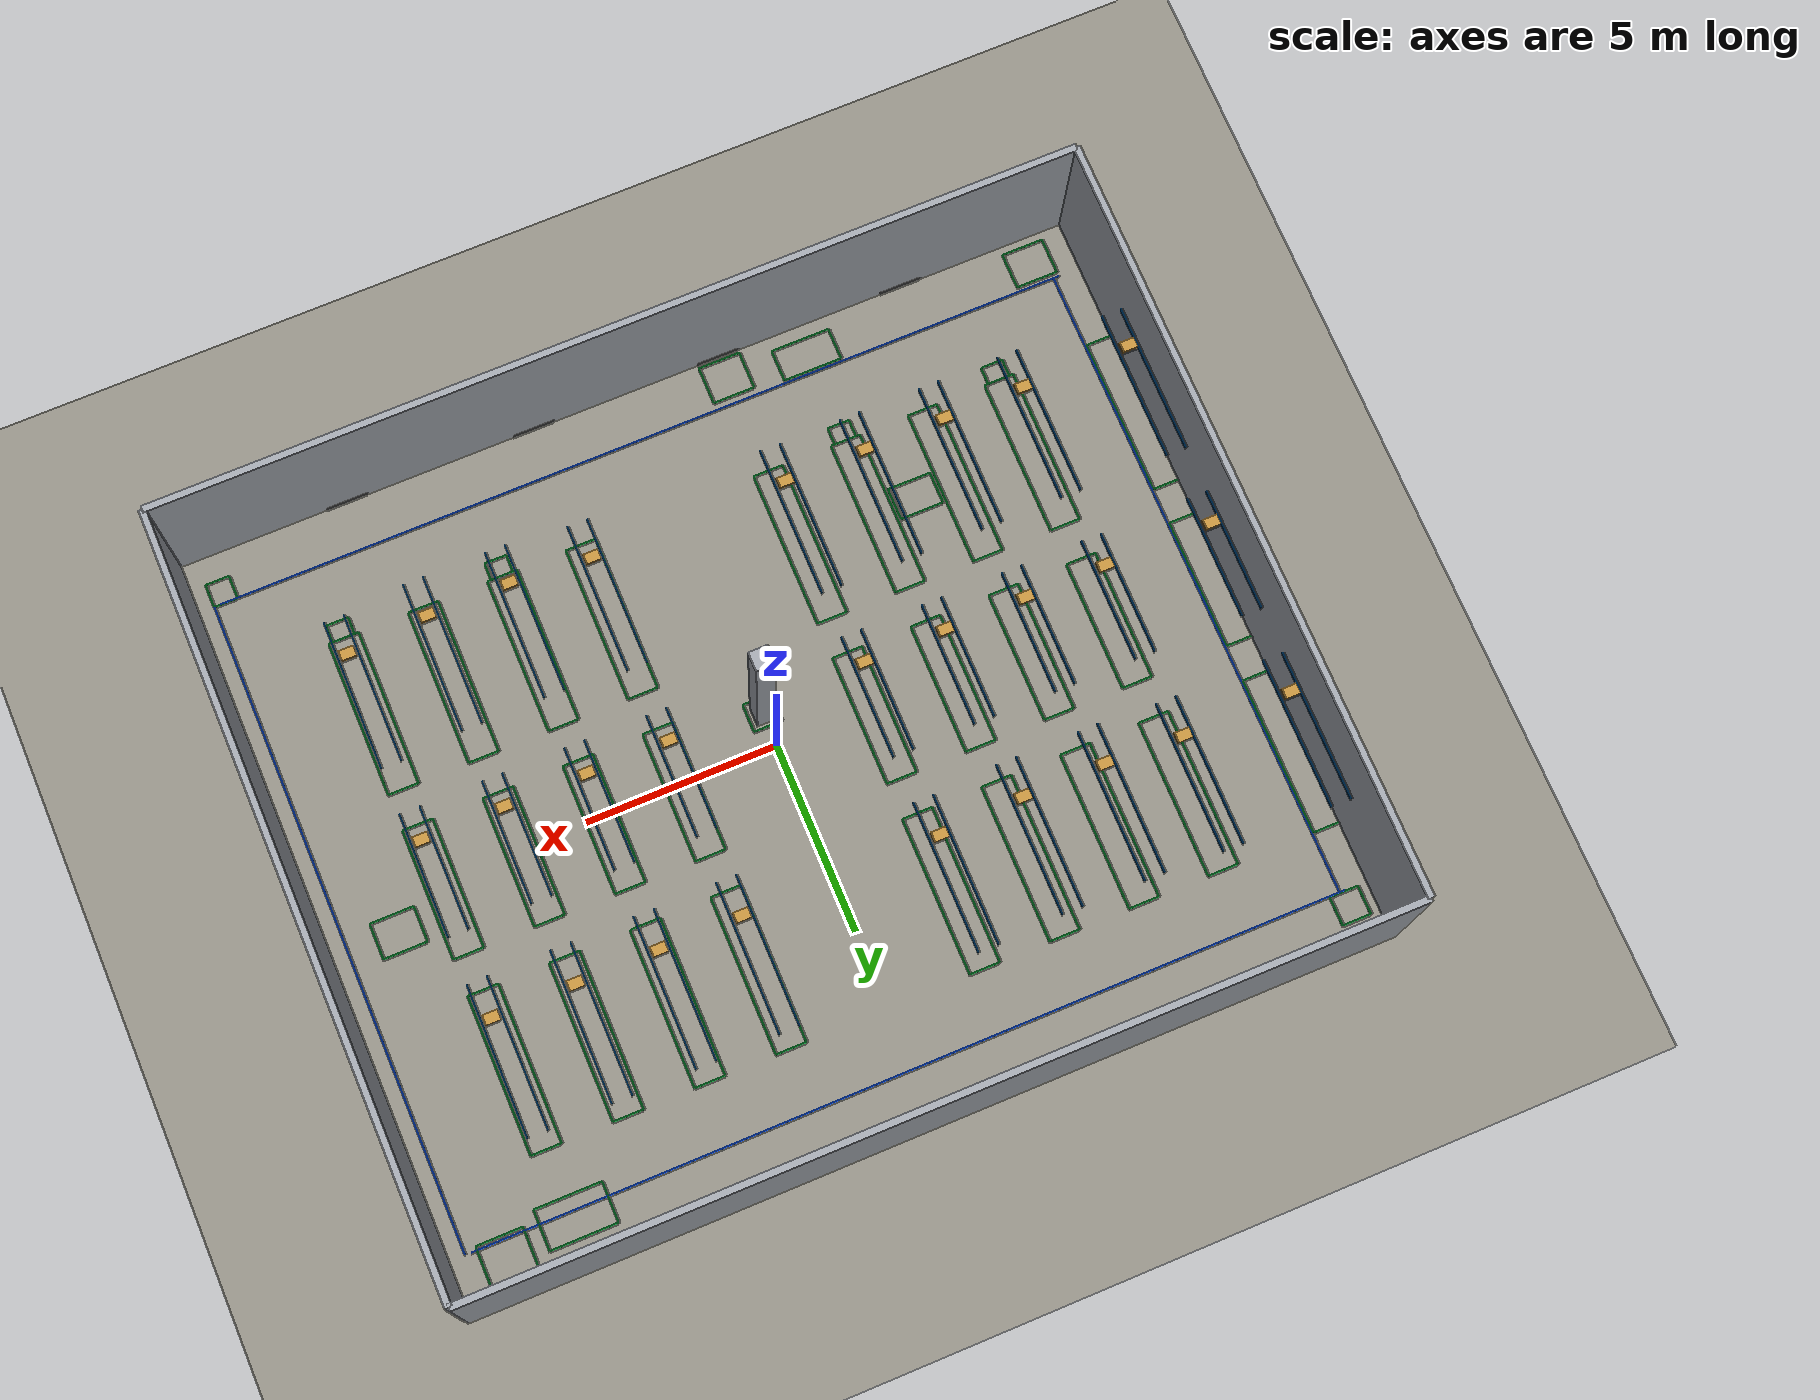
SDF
<sdf version="1.8">
 <world name="warehouse_full_4cam">
  <physics name="default_physics" type="ode">
   <max_step_size>0.001</max_step_size>
   <real_time_factor>1.0</real_time_factor>
   <real_time_update_rate>1000</real_time_update_rate>
  </physics>
  <plugin name="gz::sim::systems::Physics" filename="gz-sim-physics-system"/>
  <plugin name="gz::sim::systems::UserCommands" filename="gz-sim-user-commands-system"/>
  <plugin name="gz::sim::systems::SceneBroadcaster" filename="gz-sim-scene-broadcaster-system"/>
  <plugin name="gz::sim::systems::Contact" filename="gz-sim-contact-system"/>
  <plugin name="gz::sim::systems::Sensors" filename="gz-sim-sensors-system">
   <render_engine>ogre2</render_engine>
  </plugin>
  <gravity>0 0 -9.81</gravity>
  <magnetic_field>6e-06 2.3e-05 -4.2e-05</magnetic_field>
  <atmosphere type="adiabatic"/>
  <scene>
   <ambient>0.58 0.58 0.58 1</ambient>
   <background>0.70 0.72 0.74 1</background>
   <shadows>true</shadows>
  </scene>
  <model name="ground_plane">
   <static>true</static>
   <link name="link">
    <collision name="collision">
     <geometry><plane><normal>0 0 1</normal><size>24.5 20.5</size></plane></geometry>
    </collision>
    <visual name="visual">
     <geometry><plane><normal>0 0 1</normal><size>24.5 20.5</size></plane></geometry>
     <material>
      <ambient>0.56 0.55 0.51 1</ambient>
      <diffuse>0.56 0.55 0.51 1</diffuse>
      <specular>0.05 0.05 0.05 1</specular>
     </material>
    </visual>
   </link>
  </model>
  <model name="warehouse_walls">
   <static>true</static>
   <link name="wall_east">
    <pose>12.000 0.000 2.250 0 0 0</pose>
    <collision name="collision"><geometry><box><size>0.180 20.000 4.500</size></box></geometry></collision>
    <sensor name="contact" type="contact">
     <contact><collision>collision</collision></contact>
     <update_rate>60</update_rate>
    </sensor>
    <visual name="visual">
     <geometry><box><size>0.180 20.000 4.500</size></box></geometry>
     <material><ambient>0.62 0.64 0.67 1</ambient><diffuse>0.62 0.64 0.67 1</diffuse></material>
    </visual>
   </link>
   <link name="wall_west">
    <pose>-12.000 0.000 2.250 0 0 0</pose>
    <collision name="collision"><geometry><box><size>0.180 20.000 4.500</size></box></geometry></collision>
    <sensor name="contact" type="contact">
     <contact><collision>collision</collision></contact>
     <update_rate>60</update_rate>
    </sensor>
    <visual name="visual">
     <geometry><box><size>0.180 20.000 4.500</size></box></geometry>
     <material><ambient>0.62 0.64 0.67 1</ambient><diffuse>0.62 0.64 0.67 1</diffuse></material>
    </visual>
   </link>
   <link name="wall_north">
    <pose>0.000 10.000 2.250 0 0 0</pose>
    <collision name="collision"><geometry><box><size>24.000 0.180 4.500</size></box></geometry></collision>
    <sensor name="contact" type="contact">
     <contact><collision>collision</collision></contact>
     <update_rate>60</update_rate>
    </sensor>
    <visual name="visual">
     <geometry><box><size>24.000 0.180 4.500</size></box></geometry>
     <material><ambient>0.62 0.64 0.67 1</ambient><diffuse>0.62 0.64 0.67 1</diffuse></material>
    </visual>
   </link>
   <link name="wall_south">
    <pose>0.000 -10.000 2.250 0 0 0</pose>
    <collision name="collision"><geometry><box><size>24.000 0.180 4.500</size></box></geometry></collision>
    <sensor name="contact" type="contact">
     <contact><collision>collision</collision></contact>
     <update_rate>60</update_rate>
    </sensor>
    <visual name="visual">
     <geometry><box><size>24.000 0.180 4.500</size></box></geometry>
     <material><ambient>0.62 0.64 0.67 1</ambient><diffuse>0.62 0.64 0.67 1</diffuse></material>
    </visual>
   </link>
   <link name="south_dock_a">
    <pose>-7.500 -9.920 0.075 0 0 0</pose>
    <visual name="visual">
     <geometry><box><size>1.100 0.070 0.150</size></box></geometry>
     <material><ambient>0.50 0.50 0.50 1</ambient><diffuse>0.50 0.50 0.50 1</diffuse></material>
    </visual>
   </link>
   <link name="south_dock_b">
    <pose>-2.500 -9.920 0.075 0 0 0</pose>
    <visual name="visual">
     <geometry><box><size>1.100 0.070 0.150</size></box></geometry>
     <material><ambient>0.50 0.50 0.50 1</ambient><diffuse>0.50 0.50 0.50 1</diffuse></material>
    </visual>
   </link>
   <link name="south_dock_c">
    <pose>2.500 -9.920 0.075 0 0 0</pose>
    <visual name="visual">
     <geometry><box><size>1.100 0.070 0.150</size></box></geometry>
     <material><ambient>0.50 0.50 0.50 1</ambient><diffuse>0.50 0.50 0.50 1</diffuse></material>
    </visual>
   </link>
   <link name="south_dock_d">
    <pose>7.500 -9.920 0.075 0 0 0</pose>
    <visual name="visual">
     <geometry><box><size>1.100 0.070 0.150</size></box></geometry>
     <material><ambient>0.50 0.50 0.50 1</ambient><diffuse>0.50 0.50 0.50 1</diffuse></material>
    </visual>
   </link>
   <link name="north_dock_a">
    <pose>-5.000 9.920 0.075 0 0 0</pose>
    <visual name="visual">
     <geometry><box><size>1.100 0.070 0.150</size></box></geometry>
     <material><ambient>0.50 0.50 0.50 1</ambient><diffuse>0.50 0.50 0.50 1</diffuse></material>
    </visual>
   </link>
   <link name="north_dock_b">
    <pose>5.000 9.920 0.075 0 0 0</pose>
    <visual name="visual">
     <geometry><box><size>1.100 0.070 0.150</size></box></geometry>
     <material><ambient>0.50 0.50 0.50 1</ambient><diffuse>0.50 0.50 0.50 1</diffuse></material>
    </visual>
   </link>
  </model>
  <model name="warehouse_rack_occluders">
   <static>true</static>
   <link name="rack_W1_south">
    <pose>-8.825 -4.550 1.045 0 0 0</pose>
    <collision name="collision"><geometry><box><size>0.550 3.900 2.090</size></box></geometry></collision>
    <sensor name="contact" type="contact">
     <contact><collision>collision</collision></contact>
     <update_rate>60</update_rate>
    </sensor>
   </link>
   <link name="rail_W1_south_west">
    <pose>-9.080 -4.550 2.160 0 0 0</pose>
    <visual name="visual">
     <geometry><box><size>0.040 3.900 0.100</size></box></geometry>
     <material><ambient>0.00 0.28 0.50 1</ambient><diffuse>0.00 0.28 0.50 1</diffuse></material>
    </visual>
   </link>
   <link name="rail_W1_south_east">
    <pose>-8.570 -4.550 2.160 0 0 0</pose>
    <visual name="visual">
     <geometry><box><size>0.040 3.900 0.100</size></box></geometry>
     <material><ambient>0.00 0.28 0.50 1</ambient><diffuse>0.00 0.28 0.50 1</diffuse></material>
    </visual>
   </link>
   <link name="shelfbox_W1_south">
    <pose>-8.825 -5.525 2.290 0 0 0</pose>
    <visual name="visual">
     <geometry><box><size>0.390 0.270 0.160</size></box></geometry>
     <material><ambient>0.75 0.56 0.24 1</ambient><diffuse>0.75 0.56 0.24 1</diffuse></material>
    </visual>
   </link>
   <link name="rack_W1_mid">
    <pose>-8.825 0.200 1.045 0 0 0</pose>
    <collision name="collision"><geometry><box><size>0.550 3.200 2.090</size></box></geometry></collision>
    <sensor name="contact" type="contact">
     <contact><collision>collision</collision></contact>
     <update_rate>60</update_rate>
    </sensor>
   </link>
   <link name="rail_W1_mid_west">
    <pose>-9.080 0.200 2.160 0 0 0</pose>
    <visual name="visual">
     <geometry><box><size>0.040 3.200 0.100</size></box></geometry>
     <material><ambient>0.00 0.28 0.50 1</ambient><diffuse>0.00 0.28 0.50 1</diffuse></material>
    </visual>
   </link>
   <link name="rail_W1_mid_east">
    <pose>-8.570 0.200 2.160 0 0 0</pose>
    <visual name="visual">
     <geometry><box><size>0.040 3.200 0.100</size></box></geometry>
     <material><ambient>0.00 0.28 0.50 1</ambient><diffuse>0.00 0.28 0.50 1</diffuse></material>
    </visual>
   </link>
   <link name="shelfbox_W1_mid">
    <pose>-8.825 -0.600 2.290 0 0 0</pose>
    <visual name="visual">
     <geometry><box><size>0.390 0.270 0.160</size></box></geometry>
     <material><ambient>0.75 0.56 0.24 1</ambient><diffuse>0.75 0.56 0.24 1</diffuse></material>
    </visual>
   </link>
   <link name="rack_W1_north">
    <pose>-8.825 4.950 1.045 0 0 0</pose>
    <collision name="collision"><geometry><box><size>0.550 3.900 2.090</size></box></geometry></collision>
    <sensor name="contact" type="contact">
     <contact><collision>collision</collision></contact>
     <update_rate>60</update_rate>
    </sensor>
   </link>
   <link name="rail_W1_north_west">
    <pose>-9.080 4.950 2.160 0 0 0</pose>
    <visual name="visual">
     <geometry><box><size>0.040 3.900 0.100</size></box></geometry>
     <material><ambient>0.00 0.28 0.50 1</ambient><diffuse>0.00 0.28 0.50 1</diffuse></material>
    </visual>
   </link>
   <link name="rail_W1_north_east">
    <pose>-8.570 4.950 2.160 0 0 0</pose>
    <visual name="visual">
     <geometry><box><size>0.040 3.900 0.100</size></box></geometry>
     <material><ambient>0.00 0.28 0.50 1</ambient><diffuse>0.00 0.28 0.50 1</diffuse></material>
    </visual>
   </link>
   <link name="shelfbox_W1_north">
    <pose>-8.825 3.975 2.290 0 0 0</pose>
    <visual name="visual">
     <geometry><box><size>0.390 0.270 0.160</size></box></geometry>
     <material><ambient>0.75 0.56 0.24 1</ambient><diffuse>0.75 0.56 0.24 1</diffuse></material>
    </visual>
   </link>
   <link name="rack_W2_south">
    <pose>-6.725 -4.550 1.045 0 0 0</pose>
    <collision name="collision"><geometry><box><size>0.550 3.900 2.090</size></box></geometry></collision>
    <sensor name="contact" type="contact">
     <contact><collision>collision</collision></contact>
     <update_rate>60</update_rate>
    </sensor>
   </link>
   <link name="rail_W2_south_west">
    <pose>-6.980 -4.550 2.160 0 0 0</pose>
    <visual name="visual">
     <geometry><box><size>0.040 3.900 0.100</size></box></geometry>
     <material><ambient>0.00 0.28 0.50 1</ambient><diffuse>0.00 0.28 0.50 1</diffuse></material>
    </visual>
   </link>
   <link name="rail_W2_south_east">
    <pose>-6.470 -4.550 2.160 0 0 0</pose>
    <visual name="visual">
     <geometry><box><size>0.040 3.900 0.100</size></box></geometry>
     <material><ambient>0.00 0.28 0.50 1</ambient><diffuse>0.00 0.28 0.50 1</diffuse></material>
    </visual>
   </link>
   <link name="shelfbox_W2_south">
    <pose>-6.725 -5.525 2.290 0 0 0</pose>
    <visual name="visual">
     <geometry><box><size>0.390 0.270 0.160</size></box></geometry>
     <material><ambient>0.75 0.56 0.24 1</ambient><diffuse>0.75 0.56 0.24 1</diffuse></material>
    </visual>
   </link>
   <link name="rack_W2_mid">
    <pose>-6.725 0.200 1.045 0 0 0</pose>
    <collision name="collision"><geometry><box><size>0.550 3.200 2.090</size></box></geometry></collision>
    <sensor name="contact" type="contact">
     <contact><collision>collision</collision></contact>
     <update_rate>60</update_rate>
    </sensor>
   </link>
   <link name="rail_W2_mid_west">
    <pose>-6.980 0.200 2.160 0 0 0</pose>
    <visual name="visual">
     <geometry><box><size>0.040 3.200 0.100</size></box></geometry>
     <material><ambient>0.00 0.28 0.50 1</ambient><diffuse>0.00 0.28 0.50 1</diffuse></material>
    </visual>
   </link>
   <link name="rail_W2_mid_east">
    <pose>-6.470 0.200 2.160 0 0 0</pose>
    <visual name="visual">
     <geometry><box><size>0.040 3.200 0.100</size></box></geometry>
     <material><ambient>0.00 0.28 0.50 1</ambient><diffuse>0.00 0.28 0.50 1</diffuse></material>
    </visual>
   </link>
   <link name="shelfbox_W2_mid">
    <pose>-6.725 -0.600 2.290 0 0 0</pose>
    <visual name="visual">
     <geometry><box><size>0.390 0.270 0.160</size></box></geometry>
     <material><ambient>0.75 0.56 0.24 1</ambient><diffuse>0.75 0.56 0.24 1</diffuse></material>
    </visual>
   </link>
   <link name="rack_W2_north">
    <pose>-6.725 4.950 1.305 0 0 0</pose>
    <collision name="collision"><geometry><box><size>0.550 3.900 2.610</size></box></geometry></collision>
    <sensor name="contact" type="contact">
     <contact><collision>collision</collision></contact>
     <update_rate>60</update_rate>
    </sensor>
   </link>
   <link name="rail_W2_north_west">
    <pose>-6.980 4.950 2.680 0 0 0</pose>
    <visual name="visual">
     <geometry><box><size>0.040 3.900 0.100</size></box></geometry>
     <material><ambient>0.00 0.28 0.50 1</ambient><diffuse>0.00 0.28 0.50 1</diffuse></material>
    </visual>
   </link>
   <link name="rail_W2_north_east">
    <pose>-6.470 4.950 2.680 0 0 0</pose>
    <visual name="visual">
     <geometry><box><size>0.040 3.900 0.100</size></box></geometry>
     <material><ambient>0.00 0.28 0.50 1</ambient><diffuse>0.00 0.28 0.50 1</diffuse></material>
    </visual>
   </link>
   <link name="shelfbox_W2_north">
    <pose>-6.725 3.975 2.810 0 0 0</pose>
    <visual name="visual">
     <geometry><box><size>0.390 0.270 0.160</size></box></geometry>
     <material><ambient>0.75 0.56 0.24 1</ambient><diffuse>0.75 0.56 0.24 1</diffuse></material>
    </visual>
   </link>
   <link name="rack_W3_south">
    <pose>-4.625 -4.550 1.045 0 0 0</pose>
    <collision name="collision"><geometry><box><size>0.550 3.900 2.090</size></box></geometry></collision>
    <sensor name="contact" type="contact">
     <contact><collision>collision</collision></contact>
     <update_rate>60</update_rate>
    </sensor>
   </link>
   <link name="rail_W3_south_west">
    <pose>-4.880 -4.550 2.160 0 0 0</pose>
    <visual name="visual">
     <geometry><box><size>0.040 3.900 0.100</size></box></geometry>
     <material><ambient>0.00 0.28 0.50 1</ambient><diffuse>0.00 0.28 0.50 1</diffuse></material>
    </visual>
   </link>
   <link name="rail_W3_south_east">
    <pose>-4.370 -4.550 2.160 0 0 0</pose>
    <visual name="visual">
     <geometry><box><size>0.040 3.900 0.100</size></box></geometry>
     <material><ambient>0.00 0.28 0.50 1</ambient><diffuse>0.00 0.28 0.50 1</diffuse></material>
    </visual>
   </link>
   <link name="shelfbox_W3_south">
    <pose>-4.625 -5.525 2.290 0 0 0</pose>
    <visual name="visual">
     <geometry><box><size>0.390 0.270 0.160</size></box></geometry>
     <material><ambient>0.75 0.56 0.24 1</ambient><diffuse>0.75 0.56 0.24 1</diffuse></material>
    </visual>
   </link>
   <link name="rack_W3_mid">
    <pose>-4.625 0.200 1.045 0 0 0</pose>
    <collision name="collision"><geometry><box><size>0.550 3.200 2.090</size></box></geometry></collision>
    <sensor name="contact" type="contact">
     <contact><collision>collision</collision></contact>
     <update_rate>60</update_rate>
    </sensor>
   </link>
   <link name="rail_W3_mid_west">
    <pose>-4.880 0.200 2.160 0 0 0</pose>
    <visual name="visual">
     <geometry><box><size>0.040 3.200 0.100</size></box></geometry>
     <material><ambient>0.00 0.28 0.50 1</ambient><diffuse>0.00 0.28 0.50 1</diffuse></material>
    </visual>
   </link>
   <link name="rail_W3_mid_east">
    <pose>-4.370 0.200 2.160 0 0 0</pose>
    <visual name="visual">
     <geometry><box><size>0.040 3.200 0.100</size></box></geometry>
     <material><ambient>0.00 0.28 0.50 1</ambient><diffuse>0.00 0.28 0.50 1</diffuse></material>
    </visual>
   </link>
   <link name="shelfbox_W3_mid">
    <pose>-4.625 -0.600 2.290 0 0 0</pose>
    <visual name="visual">
     <geometry><box><size>0.390 0.270 0.160</size></box></geometry>
     <material><ambient>0.75 0.56 0.24 1</ambient><diffuse>0.75 0.56 0.24 1</diffuse></material>
    </visual>
   </link>
   <link name="rack_W3_north">
    <pose>-4.625 4.950 1.305 0 0 0</pose>
    <collision name="collision"><geometry><box><size>0.550 3.900 2.610</size></box></geometry></collision>
    <sensor name="contact" type="contact">
     <contact><collision>collision</collision></contact>
     <update_rate>60</update_rate>
    </sensor>
   </link>
   <link name="rail_W3_north_west">
    <pose>-4.880 4.950 2.680 0 0 0</pose>
    <visual name="visual">
     <geometry><box><size>0.040 3.900 0.100</size></box></geometry>
     <material><ambient>0.00 0.28 0.50 1</ambient><diffuse>0.00 0.28 0.50 1</diffuse></material>
    </visual>
   </link>
   <link name="rail_W3_north_east">
    <pose>-4.370 4.950 2.680 0 0 0</pose>
    <visual name="visual">
     <geometry><box><size>0.040 3.900 0.100</size></box></geometry>
     <material><ambient>0.00 0.28 0.50 1</ambient><diffuse>0.00 0.28 0.50 1</diffuse></material>
    </visual>
   </link>
   <link name="shelfbox_W3_north">
    <pose>-4.625 3.975 2.810 0 0 0</pose>
    <visual name="visual">
     <geometry><box><size>0.390 0.270 0.160</size></box></geometry>
     <material><ambient>0.75 0.56 0.24 1</ambient><diffuse>0.75 0.56 0.24 1</diffuse></material>
    </visual>
   </link>
   <link name="rack_W4_south">
    <pose>-2.525 -4.550 1.045 0 0 0</pose>
    <collision name="collision"><geometry><box><size>0.550 3.900 2.090</size></box></geometry></collision>
    <sensor name="contact" type="contact">
     <contact><collision>collision</collision></contact>
     <update_rate>60</update_rate>
    </sensor>
   </link>
   <link name="rail_W4_south_west">
    <pose>-2.780 -4.550 2.160 0 0 0</pose>
    <visual name="visual">
     <geometry><box><size>0.040 3.900 0.100</size></box></geometry>
     <material><ambient>0.00 0.28 0.50 1</ambient><diffuse>0.00 0.28 0.50 1</diffuse></material>
    </visual>
   </link>
   <link name="rail_W4_south_east">
    <pose>-2.270 -4.550 2.160 0 0 0</pose>
    <visual name="visual">
     <geometry><box><size>0.040 3.900 0.100</size></box></geometry>
     <material><ambient>0.00 0.28 0.50 1</ambient><diffuse>0.00 0.28 0.50 1</diffuse></material>
    </visual>
   </link>
   <link name="shelfbox_W4_south">
    <pose>-2.525 -5.525 2.290 0 0 0</pose>
    <visual name="visual">
     <geometry><box><size>0.390 0.270 0.160</size></box></geometry>
     <material><ambient>0.75 0.56 0.24 1</ambient><diffuse>0.75 0.56 0.24 1</diffuse></material>
    </visual>
   </link>
   <link name="rack_W4_mid">
    <pose>-2.525 0.200 1.045 0 0 0</pose>
    <collision name="collision"><geometry><box><size>0.550 3.200 2.090</size></box></geometry></collision>
    <sensor name="contact" type="contact">
     <contact><collision>collision</collision></contact>
     <update_rate>60</update_rate>
    </sensor>
   </link>
   <link name="rail_W4_mid_west">
    <pose>-2.780 0.200 2.160 0 0 0</pose>
    <visual name="visual">
     <geometry><box><size>0.040 3.200 0.100</size></box></geometry>
     <material><ambient>0.00 0.28 0.50 1</ambient><diffuse>0.00 0.28 0.50 1</diffuse></material>
    </visual>
   </link>
   <link name="rail_W4_mid_east">
    <pose>-2.270 0.200 2.160 0 0 0</pose>
    <visual name="visual">
     <geometry><box><size>0.040 3.200 0.100</size></box></geometry>
     <material><ambient>0.00 0.28 0.50 1</ambient><diffuse>0.00 0.28 0.50 1</diffuse></material>
    </visual>
   </link>
   <link name="shelfbox_W4_mid">
    <pose>-2.525 -0.600 2.290 0 0 0</pose>
    <visual name="visual">
     <geometry><box><size>0.390 0.270 0.160</size></box></geometry>
     <material><ambient>0.75 0.56 0.24 1</ambient><diffuse>0.75 0.56 0.24 1</diffuse></material>
    </visual>
   </link>
   <link name="rack_W4_north">
    <pose>-2.525 4.950 1.045 0 0 0</pose>
    <collision name="collision"><geometry><box><size>0.550 3.900 2.090</size></box></geometry></collision>
    <sensor name="contact" type="contact">
     <contact><collision>collision</collision></contact>
     <update_rate>60</update_rate>
    </sensor>
   </link>
   <link name="rail_W4_north_west">
    <pose>-2.780 4.950 2.160 0 0 0</pose>
    <visual name="visual">
     <geometry><box><size>0.040 3.900 0.100</size></box></geometry>
     <material><ambient>0.00 0.28 0.50 1</ambient><diffuse>0.00 0.28 0.50 1</diffuse></material>
    </visual>
   </link>
   <link name="rail_W4_north_east">
    <pose>-2.270 4.950 2.160 0 0 0</pose>
    <visual name="visual">
     <geometry><box><size>0.040 3.900 0.100</size></box></geometry>
     <material><ambient>0.00 0.28 0.50 1</ambient><diffuse>0.00 0.28 0.50 1</diffuse></material>
    </visual>
   </link>
   <link name="shelfbox_W4_north">
    <pose>-2.525 3.975 2.290 0 0 0</pose>
    <visual name="visual">
     <geometry><box><size>0.390 0.270 0.160</size></box></geometry>
     <material><ambient>0.75 0.56 0.24 1</ambient><diffuse>0.75 0.56 0.24 1</diffuse></material>
    </visual>
   </link>
   <link name="rack_E1_south">
    <pose>2.525 -4.550 1.045 0 0 0</pose>
    <collision name="collision"><geometry><box><size>0.550 3.900 2.090</size></box></geometry></collision>
    <sensor name="contact" type="contact">
     <contact><collision>collision</collision></contact>
     <update_rate>60</update_rate>
    </sensor>
   </link>
   <link name="rail_E1_south_west">
    <pose>2.270 -4.550 2.160 0 0 0</pose>
    <visual name="visual">
     <geometry><box><size>0.040 3.900 0.100</size></box></geometry>
     <material><ambient>0.00 0.28 0.50 1</ambient><diffuse>0.00 0.28 0.50 1</diffuse></material>
    </visual>
   </link>
   <link name="rail_E1_south_east">
    <pose>2.780 -4.550 2.160 0 0 0</pose>
    <visual name="visual">
     <geometry><box><size>0.040 3.900 0.100</size></box></geometry>
     <material><ambient>0.00 0.28 0.50 1</ambient><diffuse>0.00 0.28 0.50 1</diffuse></material>
    </visual>
   </link>
   <link name="shelfbox_E1_south">
    <pose>2.525 -5.525 2.290 0 0 0</pose>
    <visual name="visual">
     <geometry><box><size>0.390 0.270 0.160</size></box></geometry>
     <material><ambient>0.75 0.56 0.24 1</ambient><diffuse>0.75 0.56 0.24 1</diffuse></material>
    </visual>
   </link>
   <link name="rack_E1_mid">
    <pose>2.525 0.200 1.045 0 0 0</pose>
    <collision name="collision"><geometry><box><size>0.550 3.200 2.090</size></box></geometry></collision>
    <sensor name="contact" type="contact">
     <contact><collision>collision</collision></contact>
     <update_rate>60</update_rate>
    </sensor>
   </link>
   <link name="rail_E1_mid_west">
    <pose>2.270 0.200 2.160 0 0 0</pose>
    <visual name="visual">
     <geometry><box><size>0.040 3.200 0.100</size></box></geometry>
     <material><ambient>0.00 0.28 0.50 1</ambient><diffuse>0.00 0.28 0.50 1</diffuse></material>
    </visual>
   </link>
   <link name="rail_E1_mid_east">
    <pose>2.780 0.200 2.160 0 0 0</pose>
    <visual name="visual">
     <geometry><box><size>0.040 3.200 0.100</size></box></geometry>
     <material><ambient>0.00 0.28 0.50 1</ambient><diffuse>0.00 0.28 0.50 1</diffuse></material>
    </visual>
   </link>
   <link name="shelfbox_E1_mid">
    <pose>2.525 -0.600 2.290 0 0 0</pose>
    <visual name="visual">
     <geometry><box><size>0.390 0.270 0.160</size></box></geometry>
     <material><ambient>0.75 0.56 0.24 1</ambient><diffuse>0.75 0.56 0.24 1</diffuse></material>
    </visual>
   </link>
   <link name="rack_E1_north">
    <pose>2.525 4.950 1.045 0 0 0</pose>
    <collision name="collision"><geometry><box><size>0.550 3.900 2.090</size></box></geometry></collision>
    <sensor name="contact" type="contact">
     <contact><collision>collision</collision></contact>
     <update_rate>60</update_rate>
    </sensor>
   </link>
   <link name="rail_E1_north_west">
    <pose>2.270 4.950 2.160 0 0 0</pose>
    <visual name="visual">
     <geometry><box><size>0.040 3.900 0.100</size></box></geometry>
     <material><ambient>0.00 0.28 0.50 1</ambient><diffuse>0.00 0.28 0.50 1</diffuse></material>
    </visual>
   </link>
   <link name="rail_E1_north_east">
    <pose>2.780 4.950 2.160 0 0 0</pose>
    <visual name="visual">
     <geometry><box><size>0.040 3.900 0.100</size></box></geometry>
     <material><ambient>0.00 0.28 0.50 1</ambient><diffuse>0.00 0.28 0.50 1</diffuse></material>
    </visual>
   </link>
   <link name="shelfbox_E1_north">
    <pose>2.525 3.975 2.290 0 0 0</pose>
    <visual name="visual">
     <geometry><box><size>0.390 0.270 0.160</size></box></geometry>
     <material><ambient>0.75 0.56 0.24 1</ambient><diffuse>0.75 0.56 0.24 1</diffuse></material>
    </visual>
   </link>
   <link name="rack_E2_south">
    <pose>4.625 -4.550 1.305 0 0 0</pose>
    <collision name="collision"><geometry><box><size>0.550 3.900 2.610</size></box></geometry></collision>
    <sensor name="contact" type="contact">
     <contact><collision>collision</collision></contact>
     <update_rate>60</update_rate>
    </sensor>
   </link>
   <link name="rail_E2_south_west">
    <pose>4.370 -4.550 2.680 0 0 0</pose>
    <visual name="visual">
     <geometry><box><size>0.040 3.900 0.100</size></box></geometry>
     <material><ambient>0.00 0.28 0.50 1</ambient><diffuse>0.00 0.28 0.50 1</diffuse></material>
    </visual>
   </link>
   <link name="rail_E2_south_east">
    <pose>4.880 -4.550 2.680 0 0 0</pose>
    <visual name="visual">
     <geometry><box><size>0.040 3.900 0.100</size></box></geometry>
     <material><ambient>0.00 0.28 0.50 1</ambient><diffuse>0.00 0.28 0.50 1</diffuse></material>
    </visual>
   </link>
   <link name="shelfbox_E2_south">
    <pose>4.625 -5.525 2.810 0 0 0</pose>
    <visual name="visual">
     <geometry><box><size>0.390 0.270 0.160</size></box></geometry>
     <material><ambient>0.75 0.56 0.24 1</ambient><diffuse>0.75 0.56 0.24 1</diffuse></material>
    </visual>
   </link>
   <link name="rack_E2_mid">
    <pose>4.625 0.200 1.045 0 0 0</pose>
    <collision name="collision"><geometry><box><size>0.550 3.200 2.090</size></box></geometry></collision>
    <sensor name="contact" type="contact">
     <contact><collision>collision</collision></contact>
     <update_rate>60</update_rate>
    </sensor>
   </link>
   <link name="rail_E2_mid_west">
    <pose>4.370 0.200 2.160 0 0 0</pose>
    <visual name="visual">
     <geometry><box><size>0.040 3.200 0.100</size></box></geometry>
     <material><ambient>0.00 0.28 0.50 1</ambient><diffuse>0.00 0.28 0.50 1</diffuse></material>
    </visual>
   </link>
   <link name="rail_E2_mid_east">
    <pose>4.880 0.200 2.160 0 0 0</pose>
    <visual name="visual">
     <geometry><box><size>0.040 3.200 0.100</size></box></geometry>
     <material><ambient>0.00 0.28 0.50 1</ambient><diffuse>0.00 0.28 0.50 1</diffuse></material>
    </visual>
   </link>
   <link name="shelfbox_E2_mid">
    <pose>4.625 -0.600 2.290 0 0 0</pose>
    <visual name="visual">
     <geometry><box><size>0.390 0.270 0.160</size></box></geometry>
     <material><ambient>0.75 0.56 0.24 1</ambient><diffuse>0.75 0.56 0.24 1</diffuse></material>
    </visual>
   </link>
   <link name="rack_E2_north">
    <pose>4.625 4.950 1.045 0 0 0</pose>
    <collision name="collision"><geometry><box><size>0.550 3.900 2.090</size></box></geometry></collision>
    <sensor name="contact" type="contact">
     <contact><collision>collision</collision></contact>
     <update_rate>60</update_rate>
    </sensor>
   </link>
   <link name="rail_E2_north_west">
    <pose>4.370 4.950 2.160 0 0 0</pose>
    <visual name="visual">
     <geometry><box><size>0.040 3.900 0.100</size></box></geometry>
     <material><ambient>0.00 0.28 0.50 1</ambient><diffuse>0.00 0.28 0.50 1</diffuse></material>
    </visual>
   </link>
   <link name="rail_E2_north_east">
    <pose>4.880 4.950 2.160 0 0 0</pose>
    <visual name="visual">
     <geometry><box><size>0.040 3.900 0.100</size></box></geometry>
     <material><ambient>0.00 0.28 0.50 1</ambient><diffuse>0.00 0.28 0.50 1</diffuse></material>
    </visual>
   </link>
   <link name="shelfbox_E2_north">
    <pose>4.625 3.975 2.290 0 0 0</pose>
    <visual name="visual">
     <geometry><box><size>0.390 0.270 0.160</size></box></geometry>
     <material><ambient>0.75 0.56 0.24 1</ambient><diffuse>0.75 0.56 0.24 1</diffuse></material>
    </visual>
   </link>
   <link name="rack_E3_south">
    <pose>6.725 -4.550 1.305 0 0 0</pose>
    <collision name="collision"><geometry><box><size>0.550 3.900 2.610</size></box></geometry></collision>
    <sensor name="contact" type="contact">
     <contact><collision>collision</collision></contact>
     <update_rate>60</update_rate>
    </sensor>
   </link>
   <link name="rail_E3_south_west">
    <pose>6.470 -4.550 2.680 0 0 0</pose>
    <visual name="visual">
     <geometry><box><size>0.040 3.900 0.100</size></box></geometry>
     <material><ambient>0.00 0.28 0.50 1</ambient><diffuse>0.00 0.28 0.50 1</diffuse></material>
    </visual>
   </link>
   <link name="rail_E3_south_east">
    <pose>6.980 -4.550 2.680 0 0 0</pose>
    <visual name="visual">
     <geometry><box><size>0.040 3.900 0.100</size></box></geometry>
     <material><ambient>0.00 0.28 0.50 1</ambient><diffuse>0.00 0.28 0.50 1</diffuse></material>
    </visual>
   </link>
   <link name="shelfbox_E3_south">
    <pose>6.725 -5.525 2.810 0 0 0</pose>
    <visual name="visual">
     <geometry><box><size>0.390 0.270 0.160</size></box></geometry>
     <material><ambient>0.75 0.56 0.24 1</ambient><diffuse>0.75 0.56 0.24 1</diffuse></material>
    </visual>
   </link>
   <link name="rack_E3_mid">
    <pose>6.725 0.200 1.045 0 0 0</pose>
    <collision name="collision"><geometry><box><size>0.550 3.200 2.090</size></box></geometry></collision>
    <sensor name="contact" type="contact">
     <contact><collision>collision</collision></contact>
     <update_rate>60</update_rate>
    </sensor>
   </link>
   <link name="rail_E3_mid_west">
    <pose>6.470 0.200 2.160 0 0 0</pose>
    <visual name="visual">
     <geometry><box><size>0.040 3.200 0.100</size></box></geometry>
     <material><ambient>0.00 0.28 0.50 1</ambient><diffuse>0.00 0.28 0.50 1</diffuse></material>
    </visual>
   </link>
   <link name="rail_E3_mid_east">
    <pose>6.980 0.200 2.160 0 0 0</pose>
    <visual name="visual">
     <geometry><box><size>0.040 3.200 0.100</size></box></geometry>
     <material><ambient>0.00 0.28 0.50 1</ambient><diffuse>0.00 0.28 0.50 1</diffuse></material>
    </visual>
   </link>
   <link name="shelfbox_E3_mid">
    <pose>6.725 -0.600 2.290 0 0 0</pose>
    <visual name="visual">
     <geometry><box><size>0.390 0.270 0.160</size></box></geometry>
     <material><ambient>0.75 0.56 0.24 1</ambient><diffuse>0.75 0.56 0.24 1</diffuse></material>
    </visual>
   </link>
   <link name="rack_E3_north">
    <pose>6.725 4.950 1.045 0 0 0</pose>
    <collision name="collision"><geometry><box><size>0.550 3.900 2.090</size></box></geometry></collision>
    <sensor name="contact" type="contact">
     <contact><collision>collision</collision></contact>
     <update_rate>60</update_rate>
    </sensor>
   </link>
   <link name="rail_E3_north_west">
    <pose>6.470 4.950 2.160 0 0 0</pose>
    <visual name="visual">
     <geometry><box><size>0.040 3.900 0.100</size></box></geometry>
     <material><ambient>0.00 0.28 0.50 1</ambient><diffuse>0.00 0.28 0.50 1</diffuse></material>
    </visual>
   </link>
   <link name="rail_E3_north_east">
    <pose>6.980 4.950 2.160 0 0 0</pose>
    <visual name="visual">
     <geometry><box><size>0.040 3.900 0.100</size></box></geometry>
     <material><ambient>0.00 0.28 0.50 1</ambient><diffuse>0.00 0.28 0.50 1</diffuse></material>
    </visual>
   </link>
   <link name="shelfbox_E3_north">
    <pose>6.725 3.975 2.290 0 0 0</pose>
    <visual name="visual">
     <geometry><box><size>0.390 0.270 0.160</size></box></geometry>
     <material><ambient>0.75 0.56 0.24 1</ambient><diffuse>0.75 0.56 0.24 1</diffuse></material>
    </visual>
   </link>
   <link name="rack_E4_south">
    <pose>8.825 -4.550 1.045 0 0 0</pose>
    <collision name="collision"><geometry><box><size>0.550 3.900 2.090</size></box></geometry></collision>
    <sensor name="contact" type="contact">
     <contact><collision>collision</collision></contact>
     <update_rate>60</update_rate>
    </sensor>
   </link>
   <link name="rail_E4_south_west">
    <pose>8.570 -4.550 2.160 0 0 0</pose>
    <visual name="visual">
     <geometry><box><size>0.040 3.900 0.100</size></box></geometry>
     <material><ambient>0.00 0.28 0.50 1</ambient><diffuse>0.00 0.28 0.50 1</diffuse></material>
    </visual>
   </link>
   <link name="rail_E4_south_east">
    <pose>9.080 -4.550 2.160 0 0 0</pose>
    <visual name="visual">
     <geometry><box><size>0.040 3.900 0.100</size></box></geometry>
     <material><ambient>0.00 0.28 0.50 1</ambient><diffuse>0.00 0.28 0.50 1</diffuse></material>
    </visual>
   </link>
   <link name="shelfbox_E4_south">
    <pose>8.825 -5.525 2.290 0 0 0</pose>
    <visual name="visual">
     <geometry><box><size>0.390 0.270 0.160</size></box></geometry>
     <material><ambient>0.75 0.56 0.24 1</ambient><diffuse>0.75 0.56 0.24 1</diffuse></material>
    </visual>
   </link>
   <link name="rack_E4_mid">
    <pose>8.825 0.200 1.045 0 0 0</pose>
    <collision name="collision"><geometry><box><size>0.550 3.200 2.090</size></box></geometry></collision>
    <sensor name="contact" type="contact">
     <contact><collision>collision</collision></contact>
     <update_rate>60</update_rate>
    </sensor>
   </link>
   <link name="rail_E4_mid_west">
    <pose>8.570 0.200 2.160 0 0 0</pose>
    <visual name="visual">
     <geometry><box><size>0.040 3.200 0.100</size></box></geometry>
     <material><ambient>0.00 0.28 0.50 1</ambient><diffuse>0.00 0.28 0.50 1</diffuse></material>
    </visual>
   </link>
   <link name="rail_E4_mid_east">
    <pose>9.080 0.200 2.160 0 0 0</pose>
    <visual name="visual">
     <geometry><box><size>0.040 3.200 0.100</size></box></geometry>
     <material><ambient>0.00 0.28 0.50 1</ambient><diffuse>0.00 0.28 0.50 1</diffuse></material>
    </visual>
   </link>
   <link name="shelfbox_E4_mid">
    <pose>8.825 -0.600 2.290 0 0 0</pose>
    <visual name="visual">
     <geometry><box><size>0.390 0.270 0.160</size></box></geometry>
     <material><ambient>0.75 0.56 0.24 1</ambient><diffuse>0.75 0.56 0.24 1</diffuse></material>
    </visual>
   </link>
   <link name="rack_E4_north">
    <pose>8.825 4.950 1.045 0 0 0</pose>
    <collision name="collision"><geometry><box><size>0.550 3.900 2.090</size></box></geometry></collision>
    <sensor name="contact" type="contact">
     <contact><collision>collision</collision></contact>
     <update_rate>60</update_rate>
    </sensor>
   </link>
   <link name="rail_E4_north_west">
    <pose>8.570 4.950 2.160 0 0 0</pose>
    <visual name="visual">
     <geometry><box><size>0.040 3.900 0.100</size></box></geometry>
     <material><ambient>0.00 0.28 0.50 1</ambient><diffuse>0.00 0.28 0.50 1</diffuse></material>
    </visual>
   </link>
   <link name="rail_E4_north_east">
    <pose>9.080 4.950 2.160 0 0 0</pose>
    <visual name="visual">
     <geometry><box><size>0.040 3.900 0.100</size></box></geometry>
     <material><ambient>0.00 0.28 0.50 1</ambient><diffuse>0.00 0.28 0.50 1</diffuse></material>
    </visual>
   </link>
   <link name="shelfbox_E4_north">
    <pose>8.825 3.975 2.290 0 0 0</pose>
    <visual name="visual">
     <geometry><box><size>0.390 0.270 0.160</size></box></geometry>
     <material><ambient>0.75 0.56 0.24 1</ambient><diffuse>0.75 0.56 0.24 1</diffuse></material>
    </visual>
   </link>
   <link name="rack_W0_south">
    <pose>-11.635 -4.550 1.045 0 0 0</pose>
    <collision name="collision"><geometry><box><size>0.550 3.900 2.090</size></box></geometry></collision>
    <sensor name="contact" type="contact">
     <contact><collision>collision</collision></contact>
     <update_rate>60</update_rate>
    </sensor>
   </link>
   <link name="rail_W0_south_west">
    <pose>-11.890 -4.550 2.160 0 0 0</pose>
    <visual name="visual">
     <geometry><box><size>0.040 3.900 0.100</size></box></geometry>
     <material><ambient>0.00 0.28 0.50 1</ambient><diffuse>0.00 0.28 0.50 1</diffuse></material>
    </visual>
   </link>
   <link name="rail_W0_south_east">
    <pose>-11.380 -4.550 2.160 0 0 0</pose>
    <visual name="visual">
     <geometry><box><size>0.040 3.900 0.100</size></box></geometry>
     <material><ambient>0.00 0.28 0.50 1</ambient><diffuse>0.00 0.28 0.50 1</diffuse></material>
    </visual>
   </link>
   <link name="shelfbox_W0_south">
    <pose>-11.635 -5.525 2.290 0 0 0</pose>
    <visual name="visual">
     <geometry><box><size>0.390 0.270 0.160</size></box></geometry>
     <material><ambient>0.75 0.56 0.24 1</ambient><diffuse>0.75 0.56 0.24 1</diffuse></material>
    </visual>
   </link>
   <link name="rack_W0_mid">
    <pose>-11.635 0.200 1.045 0 0 0</pose>
    <collision name="collision"><geometry><box><size>0.550 3.200 2.090</size></box></geometry></collision>
    <sensor name="contact" type="contact">
     <contact><collision>collision</collision></contact>
     <update_rate>60</update_rate>
    </sensor>
   </link>
   <link name="rail_W0_mid_west">
    <pose>-11.890 0.200 2.160 0 0 0</pose>
    <visual name="visual">
     <geometry><box><size>0.040 3.200 0.100</size></box></geometry>
     <material><ambient>0.00 0.28 0.50 1</ambient><diffuse>0.00 0.28 0.50 1</diffuse></material>
    </visual>
   </link>
   <link name="rail_W0_mid_east">
    <pose>-11.380 0.200 2.160 0 0 0</pose>
    <visual name="visual">
     <geometry><box><size>0.040 3.200 0.100</size></box></geometry>
     <material><ambient>0.00 0.28 0.50 1</ambient><diffuse>0.00 0.28 0.50 1</diffuse></material>
    </visual>
   </link>
   <link name="shelfbox_W0_mid">
    <pose>-11.635 -0.600 2.290 0 0 0</pose>
    <visual name="visual">
     <geometry><box><size>0.390 0.270 0.160</size></box></geometry>
     <material><ambient>0.75 0.56 0.24 1</ambient><diffuse>0.75 0.56 0.24 1</diffuse></material>
    </visual>
   </link>
   <link name="rack_W0_north">
    <pose>-11.635 4.950 1.045 0 0 0</pose>
    <collision name="collision"><geometry><box><size>0.550 3.900 2.090</size></box></geometry></collision>
    <sensor name="contact" type="contact">
     <contact><collision>collision</collision></contact>
     <update_rate>60</update_rate>
    </sensor>
   </link>
   <link name="rail_W0_north_west">
    <pose>-11.890 4.950 2.160 0 0 0</pose>
    <visual name="visual">
     <geometry><box><size>0.040 3.900 0.100</size></box></geometry>
     <material><ambient>0.00 0.28 0.50 1</ambient><diffuse>0.00 0.28 0.50 1</diffuse></material>
    </visual>
   </link>
   <link name="rail_W0_north_east">
    <pose>-11.380 4.950 2.160 0 0 0</pose>
    <visual name="visual">
     <geometry><box><size>0.040 3.900 0.100</size></box></geometry>
     <material><ambient>0.00 0.28 0.50 1</ambient><diffuse>0.00 0.28 0.50 1</diffuse></material>
    </visual>
   </link>
   <link name="shelfbox_W0_north">
    <pose>-11.635 3.975 2.290 0 0 0</pose>
    <visual name="visual">
     <geometry><box><size>0.390 0.270 0.160</size></box></geometry>
     <material><ambient>0.75 0.56 0.24 1</ambient><diffuse>0.75 0.56 0.24 1</diffuse></material>
    </visual>
   </link>
   <link name="support_pillar">
    <pose>0.000 -0.900 2.600 0 0 0</pose>
    <collision name="collision"><geometry><box><size>0.500 0.500 5.200</size></box></geometry></collision>
    <sensor name="contact" type="contact">
     <contact><collision>collision</collision></contact>
     <update_rate>60</update_rate>
    </sensor>
    <visual name="visual">
     <geometry><box><size>0.500 0.500 5.200</size></box></geometry>
     <material><ambient>0.62 0.64 0.67 1</ambient><diffuse>0.62 0.64 0.67 1</diffuse></material>
    </visual>
   </link>
  </model>
  <model name="known_driveable_boundary">
   <static>true</static>
   <link name="bnd_s">
    <pose>0.000 -8.600 0.035 0 0 0</pose>
    <visual name="visual">
     <geometry><box><size>22.700 0.050 0.014</size></box></geometry>
     <material><ambient>0.05 0.30 0.85 1</ambient><diffuse>0.05 0.30 0.85 1</diffuse></material>
    </visual>
   </link>
   <link name="bnd_n">
    <pose>0.000 8.600 0.035 0 0 0</pose>
    <visual name="visual">
     <geometry><box><size>22.700 0.050 0.014</size></box></geometry>
     <material><ambient>0.05 0.30 0.85 1</ambient><diffuse>0.05 0.30 0.85 1</diffuse></material>
    </visual>
   </link>
   <link name="bnd_w">
    <pose>-11.200 0.000 0.035 0 0 0</pose>
    <visual name="visual">
     <geometry><box><size>0.050 17.200 0.014</size></box></geometry>
     <material><ambient>0.05 0.30 0.85 1</ambient><diffuse>0.05 0.30 0.85 1</diffuse></material>
    </visual>
   </link>
   <link name="bnd_e">
    <pose>11.500 0.000 0.035 0 0 0</pose>
    <visual name="visual">
     <geometry><box><size>0.050 17.200 0.014</size></box></geometry>
     <material><ambient>0.05 0.30 0.85 1</ambient><diffuse>0.05 0.30 0.85 1</diffuse></material>
    </visual>
   </link>
   <link name="nogo_W1_south_outline_s">
    <pose>-8.825 -6.620 0.035 0 0 0</pose>
    <visual name="visual">
     <geometry><box><size>0.790 0.055 0.014</size></box></geometry>
     <material><ambient>0.05 0.55 0.20 1</ambient><diffuse>0.05 0.55 0.20 1</diffuse></material>
    </visual>
   </link>
   <link name="nogo_W1_south_outline_n">
    <pose>-8.825 -2.480 0.035 0 0 0</pose>
    <visual name="visual">
     <geometry><box><size>0.790 0.055 0.014</size></box></geometry>
     <material><ambient>0.05 0.55 0.20 1</ambient><diffuse>0.05 0.55 0.20 1</diffuse></material>
    </visual>
   </link>
   <link name="nogo_W1_south_outline_w">
    <pose>-9.220 -4.550 0.035 0 0 0</pose>
    <visual name="visual">
     <geometry><box><size>0.055 4.140 0.014</size></box></geometry>
     <material><ambient>0.05 0.55 0.20 1</ambient><diffuse>0.05 0.55 0.20 1</diffuse></material>
    </visual>
   </link>
   <link name="nogo_W1_south_outline_e">
    <pose>-8.430 -4.550 0.035 0 0 0</pose>
    <visual name="visual">
     <geometry><box><size>0.055 4.140 0.014</size></box></geometry>
     <material><ambient>0.05 0.55 0.20 1</ambient><diffuse>0.05 0.55 0.20 1</diffuse></material>
    </visual>
   </link>
   <link name="nogo_W1_mid_outline_s">
    <pose>-8.825 -1.520 0.035 0 0 0</pose>
    <visual name="visual">
     <geometry><box><size>0.790 0.055 0.014</size></box></geometry>
     <material><ambient>0.05 0.55 0.20 1</ambient><diffuse>0.05 0.55 0.20 1</diffuse></material>
    </visual>
   </link>
   <link name="nogo_W1_mid_outline_n">
    <pose>-8.825 1.920 0.035 0 0 0</pose>
    <visual name="visual">
     <geometry><box><size>0.790 0.055 0.014</size></box></geometry>
     <material><ambient>0.05 0.55 0.20 1</ambient><diffuse>0.05 0.55 0.20 1</diffuse></material>
    </visual>
   </link>
   <link name="nogo_W1_mid_outline_w">
    <pose>-9.220 0.200 0.035 0 0 0</pose>
    <visual name="visual">
     <geometry><box><size>0.055 3.440 0.014</size></box></geometry>
     <material><ambient>0.05 0.55 0.20 1</ambient><diffuse>0.05 0.55 0.20 1</diffuse></material>
    </visual>
   </link>
   <link name="nogo_W1_mid_outline_e">
    <pose>-8.430 0.200 0.035 0 0 0</pose>
    <visual name="visual">
     <geometry><box><size>0.055 3.440 0.014</size></box></geometry>
     <material><ambient>0.05 0.55 0.20 1</ambient><diffuse>0.05 0.55 0.20 1</diffuse></material>
    </visual>
   </link>
   <link name="nogo_W1_north_outline_s">
    <pose>-8.825 2.880 0.035 0 0 0</pose>
    <visual name="visual">
     <geometry><box><size>0.790 0.055 0.014</size></box></geometry>
     <material><ambient>0.05 0.55 0.20 1</ambient><diffuse>0.05 0.55 0.20 1</diffuse></material>
    </visual>
   </link>
   <link name="nogo_W1_north_outline_n">
    <pose>-8.825 7.020 0.035 0 0 0</pose>
    <visual name="visual">
     <geometry><box><size>0.790 0.055 0.014</size></box></geometry>
     <material><ambient>0.05 0.55 0.20 1</ambient><diffuse>0.05 0.55 0.20 1</diffuse></material>
    </visual>
   </link>
   <link name="nogo_W1_north_outline_w">
    <pose>-9.220 4.950 0.035 0 0 0</pose>
    <visual name="visual">
     <geometry><box><size>0.055 4.140 0.014</size></box></geometry>
     <material><ambient>0.05 0.55 0.20 1</ambient><diffuse>0.05 0.55 0.20 1</diffuse></material>
    </visual>
   </link>
   <link name="nogo_W1_north_outline_e">
    <pose>-8.430 4.950 0.035 0 0 0</pose>
    <visual name="visual">
     <geometry><box><size>0.055 4.140 0.014</size></box></geometry>
     <material><ambient>0.05 0.55 0.20 1</ambient><diffuse>0.05 0.55 0.20 1</diffuse></material>
    </visual>
   </link>
   <link name="nogo_W2_south_outline_s">
    <pose>-6.725 -6.620 0.035 0 0 0</pose>
    <visual name="visual">
     <geometry><box><size>0.790 0.055 0.014</size></box></geometry>
     <material><ambient>0.05 0.55 0.20 1</ambient><diffuse>0.05 0.55 0.20 1</diffuse></material>
    </visual>
   </link>
   <link name="nogo_W2_south_outline_n">
    <pose>-6.725 -2.480 0.035 0 0 0</pose>
    <visual name="visual">
     <geometry><box><size>0.790 0.055 0.014</size></box></geometry>
     <material><ambient>0.05 0.55 0.20 1</ambient><diffuse>0.05 0.55 0.20 1</diffuse></material>
    </visual>
   </link>
   <link name="nogo_W2_south_outline_w">
    <pose>-7.120 -4.550 0.035 0 0 0</pose>
    <visual name="visual">
     <geometry><box><size>0.055 4.140 0.014</size></box></geometry>
     <material><ambient>0.05 0.55 0.20 1</ambient><diffuse>0.05 0.55 0.20 1</diffuse></material>
    </visual>
   </link>
   <link name="nogo_W2_south_outline_e">
    <pose>-6.330 -4.550 0.035 0 0 0</pose>
    <visual name="visual">
     <geometry><box><size>0.055 4.140 0.014</size></box></geometry>
     <material><ambient>0.05 0.55 0.20 1</ambient><diffuse>0.05 0.55 0.20 1</diffuse></material>
    </visual>
   </link>
   <link name="nogo_W2_mid_outline_s">
    <pose>-6.725 -1.520 0.035 0 0 0</pose>
    <visual name="visual">
     <geometry><box><size>0.790 0.055 0.014</size></box></geometry>
     <material><ambient>0.05 0.55 0.20 1</ambient><diffuse>0.05 0.55 0.20 1</diffuse></material>
    </visual>
   </link>
   <link name="nogo_W2_mid_outline_n">
    <pose>-6.725 1.920 0.035 0 0 0</pose>
    <visual name="visual">
     <geometry><box><size>0.790 0.055 0.014</size></box></geometry>
     <material><ambient>0.05 0.55 0.20 1</ambient><diffuse>0.05 0.55 0.20 1</diffuse></material>
    </visual>
   </link>
   <link name="nogo_W2_mid_outline_w">
    <pose>-7.120 0.200 0.035 0 0 0</pose>
    <visual name="visual">
     <geometry><box><size>0.055 3.440 0.014</size></box></geometry>
     <material><ambient>0.05 0.55 0.20 1</ambient><diffuse>0.05 0.55 0.20 1</diffuse></material>
    </visual>
   </link>
   <link name="nogo_W2_mid_outline_e">
    <pose>-6.330 0.200 0.035 0 0 0</pose>
    <visual name="visual">
     <geometry><box><size>0.055 3.440 0.014</size></box></geometry>
     <material><ambient>0.05 0.55 0.20 1</ambient><diffuse>0.05 0.55 0.20 1</diffuse></material>
    </visual>
   </link>
   <link name="nogo_W2_north_outline_s">
    <pose>-6.725 2.880 0.035 0 0 0</pose>
    <visual name="visual">
     <geometry><box><size>0.790 0.055 0.014</size></box></geometry>
     <material><ambient>0.05 0.55 0.20 1</ambient><diffuse>0.05 0.55 0.20 1</diffuse></material>
    </visual>
   </link>
   <link name="nogo_W2_north_outline_n">
    <pose>-6.725 7.020 0.035 0 0 0</pose>
    <visual name="visual">
     <geometry><box><size>0.790 0.055 0.014</size></box></geometry>
     <material><ambient>0.05 0.55 0.20 1</ambient><diffuse>0.05 0.55 0.20 1</diffuse></material>
    </visual>
   </link>
   <link name="nogo_W2_north_outline_w">
    <pose>-7.120 4.950 0.035 0 0 0</pose>
    <visual name="visual">
     <geometry><box><size>0.055 4.140 0.014</size></box></geometry>
     <material><ambient>0.05 0.55 0.20 1</ambient><diffuse>0.05 0.55 0.20 1</diffuse></material>
    </visual>
   </link>
   <link name="nogo_W2_north_outline_e">
    <pose>-6.330 4.950 0.035 0 0 0</pose>
    <visual name="visual">
     <geometry><box><size>0.055 4.140 0.014</size></box></geometry>
     <material><ambient>0.05 0.55 0.20 1</ambient><diffuse>0.05 0.55 0.20 1</diffuse></material>
    </visual>
   </link>
   <link name="nogo_W3_south_outline_s">
    <pose>-4.625 -6.620 0.035 0 0 0</pose>
    <visual name="visual">
     <geometry><box><size>0.790 0.055 0.014</size></box></geometry>
     <material><ambient>0.05 0.55 0.20 1</ambient><diffuse>0.05 0.55 0.20 1</diffuse></material>
    </visual>
   </link>
   <link name="nogo_W3_south_outline_n">
    <pose>-4.625 -2.480 0.035 0 0 0</pose>
    <visual name="visual">
     <geometry><box><size>0.790 0.055 0.014</size></box></geometry>
     <material><ambient>0.05 0.55 0.20 1</ambient><diffuse>0.05 0.55 0.20 1</diffuse></material>
    </visual>
   </link>
   <link name="nogo_W3_south_outline_w">
    <pose>-5.020 -4.550 0.035 0 0 0</pose>
    <visual name="visual">
     <geometry><box><size>0.055 4.140 0.014</size></box></geometry>
     <material><ambient>0.05 0.55 0.20 1</ambient><diffuse>0.05 0.55 0.20 1</diffuse></material>
    </visual>
   </link>
   <link name="nogo_W3_south_outline_e">
    <pose>-4.230 -4.550 0.035 0 0 0</pose>
    <visual name="visual">
     <geometry><box><size>0.055 4.140 0.014</size></box></geometry>
     <material><ambient>0.05 0.55 0.20 1</ambient><diffuse>0.05 0.55 0.20 1</diffuse></material>
    </visual>
   </link>
   <link name="nogo_W3_mid_outline_s">
    <pose>-4.625 -1.520 0.035 0 0 0</pose>
    <visual name="visual">
     <geometry><box><size>0.790 0.055 0.014</size></box></geometry>
     <material><ambient>0.05 0.55 0.20 1</ambient><diffuse>0.05 0.55 0.20 1</diffuse></material>
    </visual>
   </link>
   <link name="nogo_W3_mid_outline_n">
    <pose>-4.625 1.920 0.035 0 0 0</pose>
    <visual name="visual">
     <geometry><box><size>0.790 0.055 0.014</size></box></geometry>
     <material><ambient>0.05 0.55 0.20 1</ambient><diffuse>0.05 0.55 0.20 1</diffuse></material>
    </visual>
   </link>
   <link name="nogo_W3_mid_outline_w">
    <pose>-5.020 0.200 0.035 0 0 0</pose>
    <visual name="visual">
     <geometry><box><size>0.055 3.440 0.014</size></box></geometry>
     <material><ambient>0.05 0.55 0.20 1</ambient><diffuse>0.05 0.55 0.20 1</diffuse></material>
    </visual>
   </link>
   <link name="nogo_W3_mid_outline_e">
    <pose>-4.230 0.200 0.035 0 0 0</pose>
    <visual name="visual">
     <geometry><box><size>0.055 3.440 0.014</size></box></geometry>
     <material><ambient>0.05 0.55 0.20 1</ambient><diffuse>0.05 0.55 0.20 1</diffuse></material>
    </visual>
   </link>
   <link name="nogo_W3_north_outline_s">
    <pose>-4.625 2.880 0.035 0 0 0</pose>
    <visual name="visual">
     <geometry><box><size>0.790 0.055 0.014</size></box></geometry>
     <material><ambient>0.05 0.55 0.20 1</ambient><diffuse>0.05 0.55 0.20 1</diffuse></material>
    </visual>
   </link>
   <link name="nogo_W3_north_outline_n">
    <pose>-4.625 7.020 0.035 0 0 0</pose>
    <visual name="visual">
     <geometry><box><size>0.790 0.055 0.014</size></box></geometry>
     <material><ambient>0.05 0.55 0.20 1</ambient><diffuse>0.05 0.55 0.20 1</diffuse></material>
    </visual>
   </link>
   <link name="nogo_W3_north_outline_w">
    <pose>-5.020 4.950 0.035 0 0 0</pose>
    <visual name="visual">
     <geometry><box><size>0.055 4.140 0.014</size></box></geometry>
     <material><ambient>0.05 0.55 0.20 1</ambient><diffuse>0.05 0.55 0.20 1</diffuse></material>
    </visual>
   </link>
   <link name="nogo_W3_north_outline_e">
    <pose>-4.230 4.950 0.035 0 0 0</pose>
    <visual name="visual">
     <geometry><box><size>0.055 4.140 0.014</size></box></geometry>
     <material><ambient>0.05 0.55 0.20 1</ambient><diffuse>0.05 0.55 0.20 1</diffuse></material>
    </visual>
   </link>
   <link name="nogo_W4_south_outline_s">
    <pose>-2.525 -6.620 0.035 0 0 0</pose>
    <visual name="visual">
     <geometry><box><size>0.790 0.055 0.014</size></box></geometry>
     <material><ambient>0.05 0.55 0.20 1</ambient><diffuse>0.05 0.55 0.20 1</diffuse></material>
    </visual>
   </link>
   <link name="nogo_W4_south_outline_n">
    <pose>-2.525 -2.480 0.035 0 0 0</pose>
    <visual name="visual">
     <geometry><box><size>0.790 0.055 0.014</size></box></geometry>
     <material><ambient>0.05 0.55 0.20 1</ambient><diffuse>0.05 0.55 0.20 1</diffuse></material>
    </visual>
   </link>
   <link name="nogo_W4_south_outline_w">
    <pose>-2.920 -4.550 0.035 0 0 0</pose>
    <visual name="visual">
     <geometry><box><size>0.055 4.140 0.014</size></box></geometry>
     <material><ambient>0.05 0.55 0.20 1</ambient><diffuse>0.05 0.55 0.20 1</diffuse></material>
    </visual>
   </link>
   <link name="nogo_W4_south_outline_e">
    <pose>-2.130 -4.550 0.035 0 0 0</pose>
    <visual name="visual">
     <geometry><box><size>0.055 4.140 0.014</size></box></geometry>
     <material><ambient>0.05 0.55 0.20 1</ambient><diffuse>0.05 0.55 0.20 1</diffuse></material>
    </visual>
   </link>
   <link name="nogo_W4_mid_outline_s">
    <pose>-2.525 -1.520 0.035 0 0 0</pose>
    <visual name="visual">
     <geometry><box><size>0.790 0.055 0.014</size></box></geometry>
     <material><ambient>0.05 0.55 0.20 1</ambient><diffuse>0.05 0.55 0.20 1</diffuse></material>
    </visual>
   </link>
   <link name="nogo_W4_mid_outline_n">
    <pose>-2.525 1.920 0.035 0 0 0</pose>
    <visual name="visual">
     <geometry><box><size>0.790 0.055 0.014</size></box></geometry>
     <material><ambient>0.05 0.55 0.20 1</ambient><diffuse>0.05 0.55 0.20 1</diffuse></material>
    </visual>
   </link>
   <link name="nogo_W4_mid_outline_w">
    <pose>-2.920 0.200 0.035 0 0 0</pose>
    <visual name="visual">
     <geometry><box><size>0.055 3.440 0.014</size></box></geometry>
     <material><ambient>0.05 0.55 0.20 1</ambient><diffuse>0.05 0.55 0.20 1</diffuse></material>
    </visual>
   </link>
   <link name="nogo_W4_mid_outline_e">
    <pose>-2.130 0.200 0.035 0 0 0</pose>
    <visual name="visual">
     <geometry><box><size>0.055 3.440 0.014</size></box></geometry>
     <material><ambient>0.05 0.55 0.20 1</ambient><diffuse>0.05 0.55 0.20 1</diffuse></material>
    </visual>
   </link>
   <link name="nogo_W4_north_outline_s">
    <pose>-2.525 2.880 0.035 0 0 0</pose>
    <visual name="visual">
     <geometry><box><size>0.790 0.055 0.014</size></box></geometry>
     <material><ambient>0.05 0.55 0.20 1</ambient><diffuse>0.05 0.55 0.20 1</diffuse></material>
    </visual>
   </link>
   <link name="nogo_W4_north_outline_n">
    <pose>-2.525 7.020 0.035 0 0 0</pose>
    <visual name="visual">
     <geometry><box><size>0.790 0.055 0.014</size></box></geometry>
     <material><ambient>0.05 0.55 0.20 1</ambient><diffuse>0.05 0.55 0.20 1</diffuse></material>
    </visual>
   </link>
   <link name="nogo_W4_north_outline_w">
    <pose>-2.920 4.950 0.035 0 0 0</pose>
    <visual name="visual">
     <geometry><box><size>0.055 4.140 0.014</size></box></geometry>
     <material><ambient>0.05 0.55 0.20 1</ambient><diffuse>0.05 0.55 0.20 1</diffuse></material>
    </visual>
   </link>
   <link name="nogo_W4_north_outline_e">
    <pose>-2.130 4.950 0.035 0 0 0</pose>
    <visual name="visual">
     <geometry><box><size>0.055 4.140 0.014</size></box></geometry>
     <material><ambient>0.05 0.55 0.20 1</ambient><diffuse>0.05 0.55 0.20 1</diffuse></material>
    </visual>
   </link>
   <link name="nogo_E1_south_outline_s">
    <pose>2.525 -6.620 0.035 0 0 0</pose>
    <visual name="visual">
     <geometry><box><size>0.790 0.055 0.014</size></box></geometry>
     <material><ambient>0.05 0.55 0.20 1</ambient><diffuse>0.05 0.55 0.20 1</diffuse></material>
    </visual>
   </link>
   <link name="nogo_E1_south_outline_n">
    <pose>2.525 -2.480 0.035 0 0 0</pose>
    <visual name="visual">
     <geometry><box><size>0.790 0.055 0.014</size></box></geometry>
     <material><ambient>0.05 0.55 0.20 1</ambient><diffuse>0.05 0.55 0.20 1</diffuse></material>
    </visual>
   </link>
   <link name="nogo_E1_south_outline_w">
    <pose>2.130 -4.550 0.035 0 0 0</pose>
    <visual name="visual">
     <geometry><box><size>0.055 4.140 0.014</size></box></geometry>
     <material><ambient>0.05 0.55 0.20 1</ambient><diffuse>0.05 0.55 0.20 1</diffuse></material>
    </visual>
   </link>
   <link name="nogo_E1_south_outline_e">
    <pose>2.920 -4.550 0.035 0 0 0</pose>
    <visual name="visual">
     <geometry><box><size>0.055 4.140 0.014</size></box></geometry>
     <material><ambient>0.05 0.55 0.20 1</ambient><diffuse>0.05 0.55 0.20 1</diffuse></material>
    </visual>
   </link>
   <link name="nogo_E1_mid_outline_s">
    <pose>2.525 -1.520 0.035 0 0 0</pose>
    <visual name="visual">
     <geometry><box><size>0.790 0.055 0.014</size></box></geometry>
     <material><ambient>0.05 0.55 0.20 1</ambient><diffuse>0.05 0.55 0.20 1</diffuse></material>
    </visual>
   </link>
   <link name="nogo_E1_mid_outline_n">
    <pose>2.525 1.920 0.035 0 0 0</pose>
    <visual name="visual">
     <geometry><box><size>0.790 0.055 0.014</size></box></geometry>
     <material><ambient>0.05 0.55 0.20 1</ambient><diffuse>0.05 0.55 0.20 1</diffuse></material>
    </visual>
   </link>
   <link name="nogo_E1_mid_outline_w">
    <pose>2.130 0.200 0.035 0 0 0</pose>
    <visual name="visual">
     <geometry><box><size>0.055 3.440 0.014</size></box></geometry>
     <material><ambient>0.05 0.55 0.20 1</ambient><diffuse>0.05 0.55 0.20 1</diffuse></material>
    </visual>
   </link>
   <link name="nogo_E1_mid_outline_e">
    <pose>2.920 0.200 0.035 0 0 0</pose>
    <visual name="visual">
     <geometry><box><size>0.055 3.440 0.014</size></box></geometry>
     <material><ambient>0.05 0.55 0.20 1</ambient><diffuse>0.05 0.55 0.20 1</diffuse></material>
    </visual>
   </link>
   <link name="nogo_E1_north_outline_s">
    <pose>2.525 2.880 0.035 0 0 0</pose>
    <visual name="visual">
     <geometry><box><size>0.790 0.055 0.014</size></box></geometry>
     <material><ambient>0.05 0.55 0.20 1</ambient><diffuse>0.05 0.55 0.20 1</diffuse></material>
    </visual>
   </link>
   <link name="nogo_E1_north_outline_n">
    <pose>2.525 7.020 0.035 0 0 0</pose>
    <visual name="visual">
     <geometry><box><size>0.790 0.055 0.014</size></box></geometry>
     <material><ambient>0.05 0.55 0.20 1</ambient><diffuse>0.05 0.55 0.20 1</diffuse></material>
    </visual>
   </link>
   <link name="nogo_E1_north_outline_w">
    <pose>2.130 4.950 0.035 0 0 0</pose>
    <visual name="visual">
     <geometry><box><size>0.055 4.140 0.014</size></box></geometry>
     <material><ambient>0.05 0.55 0.20 1</ambient><diffuse>0.05 0.55 0.20 1</diffuse></material>
    </visual>
   </link>
   <link name="nogo_E1_north_outline_e">
    <pose>2.920 4.950 0.035 0 0 0</pose>
    <visual name="visual">
     <geometry><box><size>0.055 4.140 0.014</size></box></geometry>
     <material><ambient>0.05 0.55 0.20 1</ambient><diffuse>0.05 0.55 0.20 1</diffuse></material>
    </visual>
   </link>
   <link name="nogo_E2_south_outline_s">
    <pose>4.625 -6.620 0.035 0 0 0</pose>
    <visual name="visual">
     <geometry><box><size>0.790 0.055 0.014</size></box></geometry>
     <material><ambient>0.05 0.55 0.20 1</ambient><diffuse>0.05 0.55 0.20 1</diffuse></material>
    </visual>
   </link>
   <link name="nogo_E2_south_outline_n">
    <pose>4.625 -2.480 0.035 0 0 0</pose>
    <visual name="visual">
     <geometry><box><size>0.790 0.055 0.014</size></box></geometry>
     <material><ambient>0.05 0.55 0.20 1</ambient><diffuse>0.05 0.55 0.20 1</diffuse></material>
    </visual>
   </link>
   <link name="nogo_E2_south_outline_w">
    <pose>4.230 -4.550 0.035 0 0 0</pose>
    <visual name="visual">
     <geometry><box><size>0.055 4.140 0.014</size></box></geometry>
     <material><ambient>0.05 0.55 0.20 1</ambient><diffuse>0.05 0.55 0.20 1</diffuse></material>
    </visual>
   </link>
   <link name="nogo_E2_south_outline_e">
    <pose>5.020 -4.550 0.035 0 0 0</pose>
    <visual name="visual">
     <geometry><box><size>0.055 4.140 0.014</size></box></geometry>
     <material><ambient>0.05 0.55 0.20 1</ambient><diffuse>0.05 0.55 0.20 1</diffuse></material>
    </visual>
   </link>
   <link name="nogo_E2_mid_outline_s">
    <pose>4.625 -1.520 0.035 0 0 0</pose>
    <visual name="visual">
     <geometry><box><size>0.790 0.055 0.014</size></box></geometry>
     <material><ambient>0.05 0.55 0.20 1</ambient><diffuse>0.05 0.55 0.20 1</diffuse></material>
    </visual>
   </link>
   <link name="nogo_E2_mid_outline_n">
    <pose>4.625 1.920 0.035 0 0 0</pose>
    <visual name="visual">
     <geometry><box><size>0.790 0.055 0.014</size></box></geometry>
     <material><ambient>0.05 0.55 0.20 1</ambient><diffuse>0.05 0.55 0.20 1</diffuse></material>
    </visual>
   </link>
   <link name="nogo_E2_mid_outline_w">
    <pose>4.230 0.200 0.035 0 0 0</pose>
    <visual name="visual">
     <geometry><box><size>0.055 3.440 0.014</size></box></geometry>
     <material><ambient>0.05 0.55 0.20 1</ambient><diffuse>0.05 0.55 0.20 1</diffuse></material>
    </visual>
   </link>
   <link name="nogo_E2_mid_outline_e">
    <pose>5.020 0.200 0.035 0 0 0</pose>
    <visual name="visual">
     <geometry><box><size>0.055 3.440 0.014</size></box></geometry>
     <material><ambient>0.05 0.55 0.20 1</ambient><diffuse>0.05 0.55 0.20 1</diffuse></material>
    </visual>
   </link>
   <link name="nogo_E2_north_outline_s">
    <pose>4.625 2.880 0.035 0 0 0</pose>
    <visual name="visual">
     <geometry><box><size>0.790 0.055 0.014</size></box></geometry>
     <material><ambient>0.05 0.55 0.20 1</ambient><diffuse>0.05 0.55 0.20 1</diffuse></material>
    </visual>
   </link>
   <link name="nogo_E2_north_outline_n">
    <pose>4.625 7.020 0.035 0 0 0</pose>
    <visual name="visual">
     <geometry><box><size>0.790 0.055 0.014</size></box></geometry>
     <material><ambient>0.05 0.55 0.20 1</ambient><diffuse>0.05 0.55 0.20 1</diffuse></material>
    </visual>
   </link>
   <link name="nogo_E2_north_outline_w">
    <pose>4.230 4.950 0.035 0 0 0</pose>
    <visual name="visual">
     <geometry><box><size>0.055 4.140 0.014</size></box></geometry>
     <material><ambient>0.05 0.55 0.20 1</ambient><diffuse>0.05 0.55 0.20 1</diffuse></material>
    </visual>
   </link>
   <link name="nogo_E2_north_outline_e">
    <pose>5.020 4.950 0.035 0 0 0</pose>
    <visual name="visual">
     <geometry><box><size>0.055 4.140 0.014</size></box></geometry>
     <material><ambient>0.05 0.55 0.20 1</ambient><diffuse>0.05 0.55 0.20 1</diffuse></material>
    </visual>
   </link>
   <link name="nogo_E3_south_outline_s">
    <pose>6.725 -6.620 0.035 0 0 0</pose>
    <visual name="visual">
     <geometry><box><size>0.790 0.055 0.014</size></box></geometry>
     <material><ambient>0.05 0.55 0.20 1</ambient><diffuse>0.05 0.55 0.20 1</diffuse></material>
    </visual>
   </link>
   <link name="nogo_E3_south_outline_n">
    <pose>6.725 -2.480 0.035 0 0 0</pose>
    <visual name="visual">
     <geometry><box><size>0.790 0.055 0.014</size></box></geometry>
     <material><ambient>0.05 0.55 0.20 1</ambient><diffuse>0.05 0.55 0.20 1</diffuse></material>
    </visual>
   </link>
   <link name="nogo_E3_south_outline_w">
    <pose>6.330 -4.550 0.035 0 0 0</pose>
    <visual name="visual">
     <geometry><box><size>0.055 4.140 0.014</size></box></geometry>
     <material><ambient>0.05 0.55 0.20 1</ambient><diffuse>0.05 0.55 0.20 1</diffuse></material>
    </visual>
   </link>
   <link name="nogo_E3_south_outline_e">
    <pose>7.120 -4.550 0.035 0 0 0</pose>
    <visual name="visual">
     <geometry><box><size>0.055 4.140 0.014</size></box></geometry>
     <material><ambient>0.05 0.55 0.20 1</ambient><diffuse>0.05 0.55 0.20 1</diffuse></material>
    </visual>
   </link>
   <link name="nogo_E3_mid_outline_s">
    <pose>6.725 -1.520 0.035 0 0 0</pose>
    <visual name="visual">
     <geometry><box><size>0.790 0.055 0.014</size></box></geometry>
     <material><ambient>0.05 0.55 0.20 1</ambient><diffuse>0.05 0.55 0.20 1</diffuse></material>
    </visual>
   </link>
   <link name="nogo_E3_mid_outline_n">
    <pose>6.725 1.920 0.035 0 0 0</pose>
    <visual name="visual">
     <geometry><box><size>0.790 0.055 0.014</size></box></geometry>
     <material><ambient>0.05 0.55 0.20 1</ambient><diffuse>0.05 0.55 0.20 1</diffuse></material>
    </visual>
   </link>
   <link name="nogo_E3_mid_outline_w">
    <pose>6.330 0.200 0.035 0 0 0</pose>
    <visual name="visual">
     <geometry><box><size>0.055 3.440 0.014</size></box></geometry>
     <material><ambient>0.05 0.55 0.20 1</ambient><diffuse>0.05 0.55 0.20 1</diffuse></material>
    </visual>
   </link>
   <link name="nogo_E3_mid_outline_e">
    <pose>7.120 0.200 0.035 0 0 0</pose>
    <visual name="visual">
     <geometry><box><size>0.055 3.440 0.014</size></box></geometry>
     <material><ambient>0.05 0.55 0.20 1</ambient><diffuse>0.05 0.55 0.20 1</diffuse></material>
    </visual>
   </link>
   <link name="nogo_E3_north_outline_s">
    <pose>6.725 2.880 0.035 0 0 0</pose>
    <visual name="visual">
     <geometry><box><size>0.790 0.055 0.014</size></box></geometry>
     <material><ambient>0.05 0.55 0.20 1</ambient><diffuse>0.05 0.55 0.20 1</diffuse></material>
    </visual>
   </link>
   <link name="nogo_E3_north_outline_n">
    <pose>6.725 7.020 0.035 0 0 0</pose>
    <visual name="visual">
     <geometry><box><size>0.790 0.055 0.014</size></box></geometry>
     <material><ambient>0.05 0.55 0.20 1</ambient><diffuse>0.05 0.55 0.20 1</diffuse></material>
    </visual>
   </link>
   <link name="nogo_E3_north_outline_w">
    <pose>6.330 4.950 0.035 0 0 0</pose>
    <visual name="visual">
     <geometry><box><size>0.055 4.140 0.014</size></box></geometry>
     <material><ambient>0.05 0.55 0.20 1</ambient><diffuse>0.05 0.55 0.20 1</diffuse></material>
    </visual>
   </link>
   <link name="nogo_E3_north_outline_e">
    <pose>7.120 4.950 0.035 0 0 0</pose>
    <visual name="visual">
     <geometry><box><size>0.055 4.140 0.014</size></box></geometry>
     <material><ambient>0.05 0.55 0.20 1</ambient><diffuse>0.05 0.55 0.20 1</diffuse></material>
    </visual>
   </link>
   <link name="nogo_E4_south_outline_s">
    <pose>8.825 -6.620 0.035 0 0 0</pose>
    <visual name="visual">
     <geometry><box><size>0.790 0.055 0.014</size></box></geometry>
     <material><ambient>0.05 0.55 0.20 1</ambient><diffuse>0.05 0.55 0.20 1</diffuse></material>
    </visual>
   </link>
   <link name="nogo_E4_south_outline_n">
    <pose>8.825 -2.480 0.035 0 0 0</pose>
    <visual name="visual">
     <geometry><box><size>0.790 0.055 0.014</size></box></geometry>
     <material><ambient>0.05 0.55 0.20 1</ambient><diffuse>0.05 0.55 0.20 1</diffuse></material>
    </visual>
   </link>
   <link name="nogo_E4_south_outline_w">
    <pose>8.430 -4.550 0.035 0 0 0</pose>
    <visual name="visual">
     <geometry><box><size>0.055 4.140 0.014</size></box></geometry>
     <material><ambient>0.05 0.55 0.20 1</ambient><diffuse>0.05 0.55 0.20 1</diffuse></material>
    </visual>
   </link>
   <link name="nogo_E4_south_outline_e">
    <pose>9.220 -4.550 0.035 0 0 0</pose>
    <visual name="visual">
     <geometry><box><size>0.055 4.140 0.014</size></box></geometry>
     <material><ambient>0.05 0.55 0.20 1</ambient><diffuse>0.05 0.55 0.20 1</diffuse></material>
    </visual>
   </link>
   <link name="nogo_E4_mid_outline_s">
    <pose>8.825 -1.520 0.035 0 0 0</pose>
    <visual name="visual">
     <geometry><box><size>0.790 0.055 0.014</size></box></geometry>
     <material><ambient>0.05 0.55 0.20 1</ambient><diffuse>0.05 0.55 0.20 1</diffuse></material>
    </visual>
   </link>
   <link name="nogo_E4_mid_outline_n">
    <pose>8.825 1.920 0.035 0 0 0</pose>
    <visual name="visual">
     <geometry><box><size>0.790 0.055 0.014</size></box></geometry>
     <material><ambient>0.05 0.55 0.20 1</ambient><diffuse>0.05 0.55 0.20 1</diffuse></material>
    </visual>
   </link>
   <link name="nogo_E4_mid_outline_w">
    <pose>8.430 0.200 0.035 0 0 0</pose>
    <visual name="visual">
     <geometry><box><size>0.055 3.440 0.014</size></box></geometry>
     <material><ambient>0.05 0.55 0.20 1</ambient><diffuse>0.05 0.55 0.20 1</diffuse></material>
    </visual>
   </link>
   <link name="nogo_E4_mid_outline_e">
    <pose>9.220 0.200 0.035 0 0 0</pose>
    <visual name="visual">
     <geometry><box><size>0.055 3.440 0.014</size></box></geometry>
     <material><ambient>0.05 0.55 0.20 1</ambient><diffuse>0.05 0.55 0.20 1</diffuse></material>
    </visual>
   </link>
   <link name="nogo_E4_north_outline_s">
    <pose>8.825 2.880 0.035 0 0 0</pose>
    <visual name="visual">
     <geometry><box><size>0.790 0.055 0.014</size></box></geometry>
     <material><ambient>0.05 0.55 0.20 1</ambient><diffuse>0.05 0.55 0.20 1</diffuse></material>
    </visual>
   </link>
   <link name="nogo_E4_north_outline_n">
    <pose>8.825 7.020 0.035 0 0 0</pose>
    <visual name="visual">
     <geometry><box><size>0.790 0.055 0.014</size></box></geometry>
     <material><ambient>0.05 0.55 0.20 1</ambient><diffuse>0.05 0.55 0.20 1</diffuse></material>
    </visual>
   </link>
   <link name="nogo_E4_north_outline_w">
    <pose>8.430 4.950 0.035 0 0 0</pose>
    <visual name="visual">
     <geometry><box><size>0.055 4.140 0.014</size></box></geometry>
     <material><ambient>0.05 0.55 0.20 1</ambient><diffuse>0.05 0.55 0.20 1</diffuse></material>
    </visual>
   </link>
   <link name="nogo_E4_north_outline_e">
    <pose>9.220 4.950 0.035 0 0 0</pose>
    <visual name="visual">
     <geometry><box><size>0.055 4.140 0.014</size></box></geometry>
     <material><ambient>0.05 0.55 0.20 1</ambient><diffuse>0.05 0.55 0.20 1</diffuse></material>
    </visual>
   </link>
   <link name="nogo_W0_south_outline_s">
    <pose>-11.635 -6.620 0.035 0 0 0</pose>
    <visual name="visual">
     <geometry><box><size>0.790 0.055 0.014</size></box></geometry>
     <material><ambient>0.05 0.55 0.20 1</ambient><diffuse>0.05 0.55 0.20 1</diffuse></material>
    </visual>
   </link>
   <link name="nogo_W0_south_outline_n">
    <pose>-11.635 -2.480 0.035 0 0 0</pose>
    <visual name="visual">
     <geometry><box><size>0.790 0.055 0.014</size></box></geometry>
     <material><ambient>0.05 0.55 0.20 1</ambient><diffuse>0.05 0.55 0.20 1</diffuse></material>
    </visual>
   </link>
   <link name="nogo_W0_south_outline_w">
    <pose>-12.030 -4.550 0.035 0 0 0</pose>
    <visual name="visual">
     <geometry><box><size>0.055 4.140 0.014</size></box></geometry>
     <material><ambient>0.05 0.55 0.20 1</ambient><diffuse>0.05 0.55 0.20 1</diffuse></material>
    </visual>
   </link>
   <link name="nogo_W0_south_outline_e">
    <pose>-11.240 -4.550 0.035 0 0 0</pose>
    <visual name="visual">
     <geometry><box><size>0.055 4.140 0.014</size></box></geometry>
     <material><ambient>0.05 0.55 0.20 1</ambient><diffuse>0.05 0.55 0.20 1</diffuse></material>
    </visual>
   </link>
   <link name="nogo_W0_mid_outline_s">
    <pose>-11.635 -1.520 0.035 0 0 0</pose>
    <visual name="visual">
     <geometry><box><size>0.790 0.055 0.014</size></box></geometry>
     <material><ambient>0.05 0.55 0.20 1</ambient><diffuse>0.05 0.55 0.20 1</diffuse></material>
    </visual>
   </link>
   <link name="nogo_W0_mid_outline_n">
    <pose>-11.635 1.920 0.035 0 0 0</pose>
    <visual name="visual">
     <geometry><box><size>0.790 0.055 0.014</size></box></geometry>
     <material><ambient>0.05 0.55 0.20 1</ambient><diffuse>0.05 0.55 0.20 1</diffuse></material>
    </visual>
   </link>
   <link name="nogo_W0_mid_outline_w">
    <pose>-12.030 0.200 0.035 0 0 0</pose>
    <visual name="visual">
     <geometry><box><size>0.055 3.440 0.014</size></box></geometry>
     <material><ambient>0.05 0.55 0.20 1</ambient><diffuse>0.05 0.55 0.20 1</diffuse></material>
    </visual>
   </link>
   <link name="nogo_W0_mid_outline_e">
    <pose>-11.240 0.200 0.035 0 0 0</pose>
    <visual name="visual">
     <geometry><box><size>0.055 3.440 0.014</size></box></geometry>
     <material><ambient>0.05 0.55 0.20 1</ambient><diffuse>0.05 0.55 0.20 1</diffuse></material>
    </visual>
   </link>
   <link name="nogo_W0_north_outline_s">
    <pose>-11.635 2.880 0.035 0 0 0</pose>
    <visual name="visual">
     <geometry><box><size>0.790 0.055 0.014</size></box></geometry>
     <material><ambient>0.05 0.55 0.20 1</ambient><diffuse>0.05 0.55 0.20 1</diffuse></material>
    </visual>
   </link>
   <link name="nogo_W0_north_outline_n">
    <pose>-11.635 7.020 0.035 0 0 0</pose>
    <visual name="visual">
     <geometry><box><size>0.790 0.055 0.014</size></box></geometry>
     <material><ambient>0.05 0.55 0.20 1</ambient><diffuse>0.05 0.55 0.20 1</diffuse></material>
    </visual>
   </link>
   <link name="nogo_W0_north_outline_w">
    <pose>-12.030 4.950 0.035 0 0 0</pose>
    <visual name="visual">
     <geometry><box><size>0.055 4.140 0.014</size></box></geometry>
     <material><ambient>0.05 0.55 0.20 1</ambient><diffuse>0.05 0.55 0.20 1</diffuse></material>
    </visual>
   </link>
   <link name="nogo_W0_north_outline_e">
    <pose>-11.240 4.950 0.035 0 0 0</pose>
    <visual name="visual">
     <geometry><box><size>0.055 4.140 0.014</size></box></geometry>
     <material><ambient>0.05 0.55 0.20 1</ambient><diffuse>0.05 0.55 0.20 1</diffuse></material>
    </visual>
   </link>
   <link name="nogo_support_pillar_outline_s">
    <pose>0.000 -1.270 0.035 0 0 0</pose>
    <visual name="visual">
     <geometry><box><size>0.740 0.055 0.014</size></box></geometry>
     <material><ambient>0.05 0.55 0.20 1</ambient><diffuse>0.05 0.55 0.20 1</diffuse></material>
    </visual>
   </link>
   <link name="nogo_support_pillar_outline_n">
    <pose>0.000 -0.530 0.035 0 0 0</pose>
    <visual name="visual">
     <geometry><box><size>0.740 0.055 0.014</size></box></geometry>
     <material><ambient>0.05 0.55 0.20 1</ambient><diffuse>0.05 0.55 0.20 1</diffuse></material>
    </visual>
   </link>
   <link name="nogo_support_pillar_outline_w">
    <pose>-0.370 -0.900 0.035 0 0 0</pose>
    <visual name="visual">
     <geometry><box><size>0.055 0.740 0.014</size></box></geometry>
     <material><ambient>0.05 0.55 0.20 1</ambient><diffuse>0.05 0.55 0.20 1</diffuse></material>
    </visual>
   </link>
   <link name="nogo_support_pillar_outline_e">
    <pose>0.370 -0.900 0.035 0 0 0</pose>
    <visual name="visual">
     <geometry><box><size>0.055 0.740 0.014</size></box></geometry>
     <material><ambient>0.05 0.55 0.20 1</ambient><diffuse>0.05 0.55 0.20 1</diffuse></material>
    </visual>
   </link>
   <link name="nogo_island_stack_outline_s">
    <pose>10.200 0.330 0.035 0 0 0</pose>
    <visual name="visual">
     <geometry><box><size>1.140 0.055 0.014</size></box></geometry>
     <material><ambient>0.05 0.55 0.20 1</ambient><diffuse>0.05 0.55 0.20 1</diffuse></material>
    </visual>
   </link>
   <link name="nogo_island_stack_outline_n">
    <pose>10.200 1.270 0.035 0 0 0</pose>
    <visual name="visual">
     <geometry><box><size>1.140 0.055 0.014</size></box></geometry>
     <material><ambient>0.05 0.55 0.20 1</ambient><diffuse>0.05 0.55 0.20 1</diffuse></material>
    </visual>
   </link>
   <link name="nogo_island_stack_outline_w">
    <pose>9.630 0.800 0.035 0 0 0</pose>
    <visual name="visual">
     <geometry><box><size>0.055 0.940 0.014</size></box></geometry>
     <material><ambient>0.05 0.55 0.20 1</ambient><diffuse>0.05 0.55 0.20 1</diffuse></material>
    </visual>
   </link>
   <link name="nogo_island_stack_outline_e">
    <pose>10.770 0.800 0.035 0 0 0</pose>
    <visual name="visual">
     <geometry><box><size>0.055 0.940 0.014</size></box></geometry>
     <material><ambient>0.05 0.55 0.20 1</ambient><diffuse>0.05 0.55 0.20 1</diffuse></material>
    </visual>
   </link>
   <link name="nogo_dropped_stack_WA2_outline_s">
    <pose>-5.675 -5.020 0.035 0 0 0</pose>
    <visual name="visual">
     <geometry><box><size>1.140 0.055 0.014</size></box></geometry>
     <material><ambient>0.05 0.55 0.20 1</ambient><diffuse>0.05 0.55 0.20 1</diffuse></material>
    </visual>
   </link>
   <link name="nogo_dropped_stack_WA2_outline_n">
    <pose>-5.675 -4.180 0.035 0 0 0</pose>
    <visual name="visual">
     <geometry><box><size>1.140 0.055 0.014</size></box></geometry>
     <material><ambient>0.05 0.55 0.20 1</ambient><diffuse>0.05 0.55 0.20 1</diffuse></material>
    </visual>
   </link>
   <link name="nogo_dropped_stack_WA2_outline_w">
    <pose>-6.245 -4.600 0.035 0 0 0</pose>
    <visual name="visual">
     <geometry><box><size>0.055 0.840 0.014</size></box></geometry>
     <material><ambient>0.05 0.55 0.20 1</ambient><diffuse>0.05 0.55 0.20 1</diffuse></material>
    </visual>
   </link>
   <link name="nogo_dropped_stack_WA2_outline_e">
    <pose>-5.105 -4.600 0.035 0 0 0</pose>
    <visual name="visual">
     <geometry><box><size>0.055 0.840 0.014</size></box></geometry>
     <material><ambient>0.05 0.55 0.20 1</ambient><diffuse>0.05 0.55 0.20 1</diffuse></material>
    </visual>
   </link>
   <link name="nogo_low_crate_0_outline_s">
    <pose>-8.825 -7.080 0.035 0 0 0</pose>
    <visual name="visual">
     <geometry><box><size>0.580 0.055 0.014</size></box></geometry>
     <material><ambient>0.05 0.55 0.20 1</ambient><diffuse>0.05 0.55 0.20 1</diffuse></material>
    </visual>
   </link>
   <link name="nogo_low_crate_0_outline_n">
    <pose>-8.825 -6.620 0.035 0 0 0</pose>
    <visual name="visual">
     <geometry><box><size>0.580 0.055 0.014</size></box></geometry>
     <material><ambient>0.05 0.55 0.20 1</ambient><diffuse>0.05 0.55 0.20 1</diffuse></material>
    </visual>
   </link>
   <link name="nogo_low_crate_0_outline_w">
    <pose>-9.115 -6.850 0.035 0 0 0</pose>
    <visual name="visual">
     <geometry><box><size>0.055 0.460 0.014</size></box></geometry>
     <material><ambient>0.05 0.55 0.20 1</ambient><diffuse>0.05 0.55 0.20 1</diffuse></material>
    </visual>
   </link>
   <link name="nogo_low_crate_0_outline_e">
    <pose>-8.535 -6.850 0.035 0 0 0</pose>
    <visual name="visual">
     <geometry><box><size>0.055 0.460 0.014</size></box></geometry>
     <material><ambient>0.05 0.55 0.20 1</ambient><diffuse>0.05 0.55 0.20 1</diffuse></material>
    </visual>
   </link>
   <link name="nogo_low_crate_1_outline_s">
    <pose>-4.625 -7.080 0.035 0 0 0</pose>
    <visual name="visual">
     <geometry><box><size>0.580 0.055 0.014</size></box></geometry>
     <material><ambient>0.05 0.55 0.20 1</ambient><diffuse>0.05 0.55 0.20 1</diffuse></material>
    </visual>
   </link>
   <link name="nogo_low_crate_1_outline_n">
    <pose>-4.625 -6.620 0.035 0 0 0</pose>
    <visual name="visual">
     <geometry><box><size>0.580 0.055 0.014</size></box></geometry>
     <material><ambient>0.05 0.55 0.20 1</ambient><diffuse>0.05 0.55 0.20 1</diffuse></material>
    </visual>
   </link>
   <link name="nogo_low_crate_1_outline_w">
    <pose>-4.915 -6.850 0.035 0 0 0</pose>
    <visual name="visual">
     <geometry><box><size>0.055 0.460 0.014</size></box></geometry>
     <material><ambient>0.05 0.55 0.20 1</ambient><diffuse>0.05 0.55 0.20 1</diffuse></material>
    </visual>
   </link>
   <link name="nogo_low_crate_1_outline_e">
    <pose>-4.335 -6.850 0.035 0 0 0</pose>
    <visual name="visual">
     <geometry><box><size>0.055 0.460 0.014</size></box></geometry>
     <material><ambient>0.05 0.55 0.20 1</ambient><diffuse>0.05 0.55 0.20 1</diffuse></material>
    </visual>
   </link>
   <link name="nogo_low_crate_2_outline_s">
    <pose>4.625 -7.080 0.035 0 0 0</pose>
    <visual name="visual">
     <geometry><box><size>0.580 0.055 0.014</size></box></geometry>
     <material><ambient>0.05 0.55 0.20 1</ambient><diffuse>0.05 0.55 0.20 1</diffuse></material>
    </visual>
   </link>
   <link name="nogo_low_crate_2_outline_n">
    <pose>4.625 -6.620 0.035 0 0 0</pose>
    <visual name="visual">
     <geometry><box><size>0.580 0.055 0.014</size></box></geometry>
     <material><ambient>0.05 0.55 0.20 1</ambient><diffuse>0.05 0.55 0.20 1</diffuse></material>
    </visual>
   </link>
   <link name="nogo_low_crate_2_outline_w">
    <pose>4.335 -6.850 0.035 0 0 0</pose>
    <visual name="visual">
     <geometry><box><size>0.055 0.460 0.014</size></box></geometry>
     <material><ambient>0.05 0.55 0.20 1</ambient><diffuse>0.05 0.55 0.20 1</diffuse></material>
    </visual>
   </link>
   <link name="nogo_low_crate_2_outline_e">
    <pose>4.915 -6.850 0.035 0 0 0</pose>
    <visual name="visual">
     <geometry><box><size>0.055 0.460 0.014</size></box></geometry>
     <material><ambient>0.05 0.55 0.20 1</ambient><diffuse>0.05 0.55 0.20 1</diffuse></material>
    </visual>
   </link>
   <link name="nogo_low_crate_3_outline_s">
    <pose>8.825 -7.080 0.035 0 0 0</pose>
    <visual name="visual">
     <geometry><box><size>0.580 0.055 0.014</size></box></geometry>
     <material><ambient>0.05 0.55 0.20 1</ambient><diffuse>0.05 0.55 0.20 1</diffuse></material>
    </visual>
   </link>
   <link name="nogo_low_crate_3_outline_n">
    <pose>8.825 -6.620 0.035 0 0 0</pose>
    <visual name="visual">
     <geometry><box><size>0.580 0.055 0.014</size></box></geometry>
     <material><ambient>0.05 0.55 0.20 1</ambient><diffuse>0.05 0.55 0.20 1</diffuse></material>
    </visual>
   </link>
   <link name="nogo_low_crate_3_outline_w">
    <pose>8.535 -6.850 0.035 0 0 0</pose>
    <visual name="visual">
     <geometry><box><size>0.055 0.460 0.014</size></box></geometry>
     <material><ambient>0.05 0.55 0.20 1</ambient><diffuse>0.05 0.55 0.20 1</diffuse></material>
    </visual>
   </link>
   <link name="nogo_low_crate_3_outline_e">
    <pose>9.115 -6.850 0.035 0 0 0</pose>
    <visual name="visual">
     <geometry><box><size>0.055 0.460 0.014</size></box></geometry>
     <material><ambient>0.05 0.55 0.20 1</ambient><diffuse>0.05 0.55 0.20 1</diffuse></material>
    </visual>
   </link>
   <link name="nogo_bucket_dock_outline_s">
    <pose>11.200 -9.210 0.035 0 0 0</pose>
    <visual name="visual">
     <geometry><box><size>0.620 0.055 0.014</size></box></geometry>
     <material><ambient>0.05 0.55 0.20 1</ambient><diffuse>0.05 0.55 0.20 1</diffuse></material>
    </visual>
   </link>
   <link name="nogo_bucket_dock_outline_n">
    <pose>11.200 -8.590 0.035 0 0 0</pose>
    <visual name="visual">
     <geometry><box><size>0.620 0.055 0.014</size></box></geometry>
     <material><ambient>0.05 0.55 0.20 1</ambient><diffuse>0.05 0.55 0.20 1</diffuse></material>
    </visual>
   </link>
   <link name="nogo_bucket_dock_outline_w">
    <pose>10.890 -8.900 0.035 0 0 0</pose>
    <visual name="visual">
     <geometry><box><size>0.055 0.620 0.014</size></box></geometry>
     <material><ambient>0.05 0.55 0.20 1</ambient><diffuse>0.05 0.55 0.20 1</diffuse></material>
    </visual>
   </link>
   <link name="nogo_bucket_dock_outline_e">
    <pose>11.510 -8.900 0.035 0 0 0</pose>
    <visual name="visual">
     <geometry><box><size>0.055 0.620 0.014</size></box></geometry>
     <material><ambient>0.05 0.55 0.20 1</ambient><diffuse>0.05 0.55 0.20 1</diffuse></material>
    </visual>
   </link>
   <link name="nogo_trashcan_nw_outline_s">
    <pose>-11.300 8.625 0.035 0 0 0</pose>
    <visual name="visual">
     <geometry><box><size>0.750 0.055 0.014</size></box></geometry>
     <material><ambient>0.05 0.55 0.20 1</ambient><diffuse>0.05 0.55 0.20 1</diffuse></material>
    </visual>
   </link>
   <link name="nogo_trashcan_nw_outline_n">
    <pose>-11.300 9.375 0.035 0 0 0</pose>
    <visual name="visual">
     <geometry><box><size>0.750 0.055 0.014</size></box></geometry>
     <material><ambient>0.05 0.55 0.20 1</ambient><diffuse>0.05 0.55 0.20 1</diffuse></material>
    </visual>
   </link>
   <link name="nogo_trashcan_nw_outline_w">
    <pose>-11.675 9.000 0.035 0 0 0</pose>
    <visual name="visual">
     <geometry><box><size>0.055 0.750 0.014</size></box></geometry>
     <material><ambient>0.05 0.55 0.20 1</ambient><diffuse>0.05 0.55 0.20 1</diffuse></material>
    </visual>
   </link>
   <link name="nogo_trashcan_nw_outline_e">
    <pose>-10.925 9.000 0.035 0 0 0</pose>
    <visual name="visual">
     <geometry><box><size>0.055 0.750 0.014</size></box></geometry>
     <material><ambient>0.05 0.55 0.20 1</ambient><diffuse>0.05 0.55 0.20 1</diffuse></material>
    </visual>
   </link>
   <link name="nogo_clutterA_sw_outline_s">
    <pose>-10.800 -9.675 0.035 0 0 0</pose>
    <visual name="visual">
     <geometry><box><size>1.100 0.055 0.014</size></box></geometry>
     <material><ambient>0.05 0.55 0.20 1</ambient><diffuse>0.05 0.55 0.20 1</diffuse></material>
    </visual>
   </link>
   <link name="nogo_clutterA_sw_outline_n">
    <pose>-10.800 -8.725 0.035 0 0 0</pose>
    <visual name="visual">
     <geometry><box><size>1.100 0.055 0.014</size></box></geometry>
     <material><ambient>0.05 0.55 0.20 1</ambient><diffuse>0.05 0.55 0.20 1</diffuse></material>
    </visual>
   </link>
   <link name="nogo_clutterA_sw_outline_w">
    <pose>-11.350 -9.200 0.035 0 0 0</pose>
    <visual name="visual">
     <geometry><box><size>0.055 0.950 0.014</size></box></geometry>
     <material><ambient>0.05 0.55 0.20 1</ambient><diffuse>0.05 0.55 0.20 1</diffuse></material>
    </visual>
   </link>
   <link name="nogo_clutterA_sw_outline_e">
    <pose>-10.250 -9.200 0.035 0 0 0</pose>
    <visual name="visual">
     <geometry><box><size>0.055 0.950 0.014</size></box></geometry>
     <material><ambient>0.05 0.55 0.20 1</ambient><diffuse>0.05 0.55 0.20 1</diffuse></material>
    </visual>
   </link>
   <link name="nogo_clutterC_ne_outline_s">
    <pose>10.600 8.500 0.035 0 0 0</pose>
    <visual name="visual">
     <geometry><box><size>1.200 0.055 0.014</size></box></geometry>
     <material><ambient>0.05 0.55 0.20 1</ambient><diffuse>0.05 0.55 0.20 1</diffuse></material>
    </visual>
   </link>
   <link name="nogo_clutterC_ne_outline_n">
    <pose>10.600 9.500 0.035 0 0 0</pose>
    <visual name="visual">
     <geometry><box><size>1.200 0.055 0.014</size></box></geometry>
     <material><ambient>0.05 0.55 0.20 1</ambient><diffuse>0.05 0.55 0.20 1</diffuse></material>
    </visual>
   </link>
   <link name="nogo_clutterC_ne_outline_w">
    <pose>10.000 9.000 0.035 0 0 0</pose>
    <visual name="visual">
     <geometry><box><size>0.055 1.000 0.014</size></box></geometry>
     <material><ambient>0.05 0.55 0.20 1</ambient><diffuse>0.05 0.55 0.20 1</diffuse></material>
    </visual>
   </link>
   <link name="nogo_clutterC_ne_outline_e">
    <pose>11.200 9.000 0.035 0 0 0</pose>
    <visual name="visual">
     <geometry><box><size>0.055 1.000 0.014</size></box></geometry>
     <material><ambient>0.05 0.55 0.20 1</ambient><diffuse>0.05 0.55 0.20 1</diffuse></material>
    </visual>
   </link>
   <link name="nogo_clutterD_dock_outline_s">
    <pose>-2.500 -9.800 0.035 0 0 0</pose>
    <visual name="visual">
     <geometry><box><size>1.100 0.055 0.014</size></box></geometry>
     <material><ambient>0.05 0.55 0.20 1</ambient><diffuse>0.05 0.55 0.20 1</diffuse></material>
    </visual>
   </link>
   <link name="nogo_clutterD_dock_outline_n">
    <pose>-2.500 -8.800 0.035 0 0 0</pose>
    <visual name="visual">
     <geometry><box><size>1.100 0.055 0.014</size></box></geometry>
     <material><ambient>0.05 0.55 0.20 1</ambient><diffuse>0.05 0.55 0.20 1</diffuse></material>
    </visual>
   </link>
   <link name="nogo_clutterD_dock_outline_w">
    <pose>-3.050 -9.300 0.035 0 0 0</pose>
    <visual name="visual">
     <geometry><box><size>0.055 1.000 0.014</size></box></geometry>
     <material><ambient>0.05 0.55 0.20 1</ambient><diffuse>0.05 0.55 0.20 1</diffuse></material>
    </visual>
   </link>
   <link name="nogo_clutterD_dock_outline_e">
    <pose>-1.950 -9.300 0.035 0 0 0</pose>
    <visual name="visual">
     <geometry><box><size>0.055 1.000 0.014</size></box></geometry>
     <material><ambient>0.05 0.55 0.20 1</ambient><diffuse>0.05 0.55 0.20 1</diffuse></material>
    </visual>
   </link>
   <link name="nogo_palletjack_apron_outline_s">
    <pose>-4.600 -9.525 0.035 0 0 0</pose>
    <visual name="visual">
     <geometry><box><size>1.550 0.055 0.014</size></box></geometry>
     <material><ambient>0.05 0.55 0.20 1</ambient><diffuse>0.05 0.55 0.20 1</diffuse></material>
    </visual>
   </link>
   <link name="nogo_palletjack_apron_outline_n">
    <pose>-4.600 -8.675 0.035 0 0 0</pose>
    <visual name="visual">
     <geometry><box><size>1.550 0.055 0.014</size></box></geometry>
     <material><ambient>0.05 0.55 0.20 1</ambient><diffuse>0.05 0.55 0.20 1</diffuse></material>
    </visual>
   </link>
   <link name="nogo_palletjack_apron_outline_w">
    <pose>-5.375 -9.100 0.035 0 0 0</pose>
    <visual name="visual">
     <geometry><box><size>0.055 0.850 0.014</size></box></geometry>
     <material><ambient>0.05 0.55 0.20 1</ambient><diffuse>0.05 0.55 0.20 1</diffuse></material>
    </visual>
   </link>
   <link name="nogo_palletjack_apron_outline_e">
    <pose>-3.825 -9.100 0.035 0 0 0</pose>
    <visual name="visual">
     <geometry><box><size>0.055 0.850 0.014</size></box></geometry>
     <material><ambient>0.05 0.55 0.20 1</ambient><diffuse>0.05 0.55 0.20 1</diffuse></material>
    </visual>
   </link>
   <link name="nogo_desk_qc_ne_outline_s">
    <pose>8.750 8.225 0.035 0 0 0</pose>
    <visual name="visual">
     <geometry><box><size>1.750 0.055 0.014</size></box></geometry>
     <material><ambient>0.05 0.55 0.20 1</ambient><diffuse>0.05 0.55 0.20 1</diffuse></material>
    </visual>
   </link>
   <link name="nogo_desk_qc_ne_outline_n">
    <pose>8.750 9.275 0.035 0 0 0</pose>
    <visual name="visual">
     <geometry><box><size>1.750 0.055 0.014</size></box></geometry>
     <material><ambient>0.05 0.55 0.20 1</ambient><diffuse>0.05 0.55 0.20 1</diffuse></material>
    </visual>
   </link>
   <link name="nogo_desk_qc_ne_outline_w">
    <pose>7.875 8.750 0.035 0 0 0</pose>
    <visual name="visual">
     <geometry><box><size>0.055 1.050 0.014</size></box></geometry>
     <material><ambient>0.05 0.55 0.20 1</ambient><diffuse>0.05 0.55 0.20 1</diffuse></material>
    </visual>
   </link>
   <link name="nogo_desk_qc_ne_outline_e">
    <pose>9.625 8.750 0.035 0 0 0</pose>
    <visual name="visual">
     <geometry><box><size>0.055 1.050 0.014</size></box></geometry>
     <material><ambient>0.05 0.55 0.20 1</ambient><diffuse>0.05 0.55 0.20 1</diffuse></material>
    </visual>
   </link>
  </model>
  <include>
   <name>external_camera</name>
   <uri>model://external_camera</uri>
   <pose>-6.00 -10.00 6.10 0 0.92 1.5708</pose>
  </include>
  <include>
   <name>external_camera_b</name>
   <uri>model://external_camera_b</uri>
   <pose>-6.00 10.00 6.10 0 0.92 -1.5708</pose>
  </include>
  <include>
   <name>external_camera_c</name>
   <uri>model://external_camera_c</uri>
   <pose>6.00 -10.00 6.10 0 0.92 1.5708</pose>
  </include>
  <include>
   <name>external_camera_d</name>
   <uri>model://external_camera_d</uri>
   <pose>6.00 10.00 6.10 0 0.92 -1.5708</pose>
  </include>
  <light name="sun" type="directional">
   <pose>0 0 12 0 0 0</pose>
   <intensity>0.74</intensity>
   <direction>-0.25 0.15 -1</direction>
  </light>
  <light name="south_overhead_light" type="point">
   <pose>0 -6.0 5.1 0 0 0</pose>
   <intensity>0.60</intensity>
   <attenuation>
    <range>18</range>
    <constant>0.45</constant>
    <linear>0.06</linear>
    <quadratic>0.010</quadratic>
   </attenuation>
  </light>
  <light name="center_overhead_light" type="point">
   <pose>0 0.5 5.2 0 0 0</pose>
   <intensity>0.65</intensity>
   <attenuation>
    <range>18</range>
    <constant>0.45</constant>
    <linear>0.06</linear>
    <quadratic>0.010</quadratic>
   </attenuation>
  </light>
  <light name="north_overhead_light" type="point">
   <pose>0 6.5 5.1 0 0 0</pose>
   <intensity>0.62</intensity>
   <attenuation>
    <range>18</range>
    <constant>0.45</constant>
    <linear>0.06</linear>
    <quadratic>0.010</quadratic>
   </attenuation>
  </light>
 </world>
</sdf>

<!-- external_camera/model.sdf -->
<sdf version="1.6">
  <model name="external_camera">
    <static>true</static>
    <pose>0 0 0 0 0 0</pose>
    <link name="link">
      <sensor name="camera" type="camera">
        <camera>
          <horizontal_fov>1.5708</horizontal_fov> <!-- 90 degrees -->
          <image>
            <width>1280</width>
            <height>720</height>
          </image>
          <clip>
            <near>0.1</near>
            <far>100</far>
          </clip>
        </camera>
        <always_on>1</always_on>
        <update_rate>5</update_rate>
        <visualize>false</visualize>
        <topic>external_camera/image_raw</topic>
      </sensor>
      <sensor name="depth_camera" type="depth_camera">
        <camera>
          <horizontal_fov>1.5708</horizontal_fov>
          <image><width>1280</width><height>720</height><format>R_FLOAT32</format></image>
          <clip><near>0.1</near><far>100</far></clip>
        </camera>
        <always_on>0</always_on>
        <update_rate>5</update_rate>
        <visualize>false</visualize>
        <topic>external_camera/depth</topic>
      </sensor>
      <sensor name="segmentation_camera" type="segmentation">
        <camera>
          <segmentation_type>semantic</segmentation_type>
          <horizontal_fov>1.5708</horizontal_fov>
          <image>
            <width>1280</width>
            <height>720</height>
          </image>
          <clip>
            <near>0.1</near>
            <far>100</far>
          </clip>
        </camera>
        <always_on>0</always_on>
        <update_rate>1</update_rate>
        <visualize>false</visualize>
        <topic>external_camera/segmentation</topic>
      </sensor>
    </link>
  </model>
</sdf>

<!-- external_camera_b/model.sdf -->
<sdf version="1.6">
  <model name="external_camera_b">
    <static>true</static>
    <pose>0 0 0 0 0 0</pose>
    <link name="link">
      <sensor name="camera" type="camera">
        <camera>
          <horizontal_fov>1.5708</horizontal_fov>
          <image>
            <width>1280</width>
            <height>720</height>
          </image>
          <clip>
            <near>0.1</near>
            <far>100</far>
          </clip>
        </camera>
        <always_on>1</always_on>
        <update_rate>5</update_rate>
        <visualize>false</visualize>
        <topic>external_camera_b/image_raw</topic>
      </sensor>
      <sensor name="depth_camera" type="depth_camera">
        <camera>
          <horizontal_fov>1.5708</horizontal_fov>
          <image><width>1280</width><height>720</height><format>R_FLOAT32</format></image>
          <clip><near>0.1</near><far>100</far></clip>
        </camera>
        <always_on>0</always_on>
        <update_rate>5</update_rate>
        <visualize>false</visualize>
        <topic>external_camera_b/depth</topic>
      </sensor>
      <sensor name="segmentation_camera" type="segmentation">
        <camera>
          <segmentation_type>semantic</segmentation_type>
          <horizontal_fov>1.5708</horizontal_fov>
          <image>
            <width>1280</width>
            <height>720</height>
          </image>
          <clip>
            <near>0.1</near>
            <far>100</far>
          </clip>
        </camera>
        <always_on>0</always_on>
        <update_rate>1</update_rate>
        <visualize>false</visualize>
        <topic>external_camera_b/segmentation</topic>
      </sensor>
    </link>
  </model>
</sdf>

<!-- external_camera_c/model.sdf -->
<sdf version="1.6">
  <model name="external_camera_c">
    <static>true</static>
    <pose>0 0 0 0 0 0</pose>
    <link name="link">
      <sensor name="camera" type="camera">
        <camera>
          <horizontal_fov>1.5708</horizontal_fov>
          <image>
            <width>1280</width>
            <height>720</height>
          </image>
          <clip>
            <near>0.1</near>
            <far>100</far>
          </clip>
        </camera>
        <always_on>1</always_on>
        <update_rate>5</update_rate>
        <visualize>false</visualize>
        <topic>external_camera_c/image_raw</topic>
      </sensor>
      <sensor name="depth_camera" type="depth_camera">
        <camera>
          <horizontal_fov>1.5708</horizontal_fov>
          <image><width>1280</width><height>720</height><format>R_FLOAT32</format></image>
          <clip><near>0.1</near><far>100</far></clip>
        </camera>
        <always_on>0</always_on>
        <update_rate>5</update_rate>
        <visualize>false</visualize>
        <topic>external_camera_c/depth</topic>
      </sensor>
      <sensor name="segmentation_camera" type="segmentation">
        <camera>
          <segmentation_type>semantic</segmentation_type>
          <horizontal_fov>1.5708</horizontal_fov>
          <image>
            <width>1280</width>
            <height>720</height>
          </image>
          <clip>
            <near>0.1</near>
            <far>100</far>
          </clip>
        </camera>
        <always_on>0</always_on>
        <update_rate>1</update_rate>
        <visualize>false</visualize>
        <topic>external_camera_c/segmentation</topic>
      </sensor>
    </link>
  </model>
</sdf>

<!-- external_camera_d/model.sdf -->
<sdf version="1.6">
  <model name="external_camera_d">
    <static>true</static>
    <pose>0 0 0 0 0 0</pose>
    <link name="link">
      <sensor name="camera" type="camera">
        <camera>
          <horizontal_fov>1.5708</horizontal_fov>
          <image>
            <width>1280</width>
            <height>720</height>
          </image>
          <clip>
            <near>0.1</near>
            <far>100</far>
          </clip>
        </camera>
        <always_on>1</always_on>
        <update_rate>5</update_rate>
        <visualize>false</visualize>
        <topic>external_camera_d/image_raw</topic>
      </sensor>
      <sensor name="depth_camera" type="depth_camera">
        <camera>
          <horizontal_fov>1.5708</horizontal_fov>
          <image><width>1280</width><height>720</height><format>R_FLOAT32</format></image>
          <clip><near>0.1</near><far>100</far></clip>
        </camera>
        <always_on>0</always_on>
        <update_rate>5</update_rate>
        <visualize>false</visualize>
        <topic>external_camera_d/depth</topic>
      </sensor>
      <sensor name="segmentation_camera" type="segmentation">
        <camera>
          <segmentation_type>semantic</segmentation_type>
          <horizontal_fov>1.5708</horizontal_fov>
          <image>
            <width>1280</width>
            <height>720</height>
          </image>
          <clip>
            <near>0.1</near>
            <far>100</far>
          </clip>
        </camera>
        <always_on>0</always_on>
        <update_rate>1</update_rate>
        <visualize>false</visualize>
        <topic>external_camera_d/segmentation</topic>
      </sensor>
    </link>
  </model>
</sdf>
